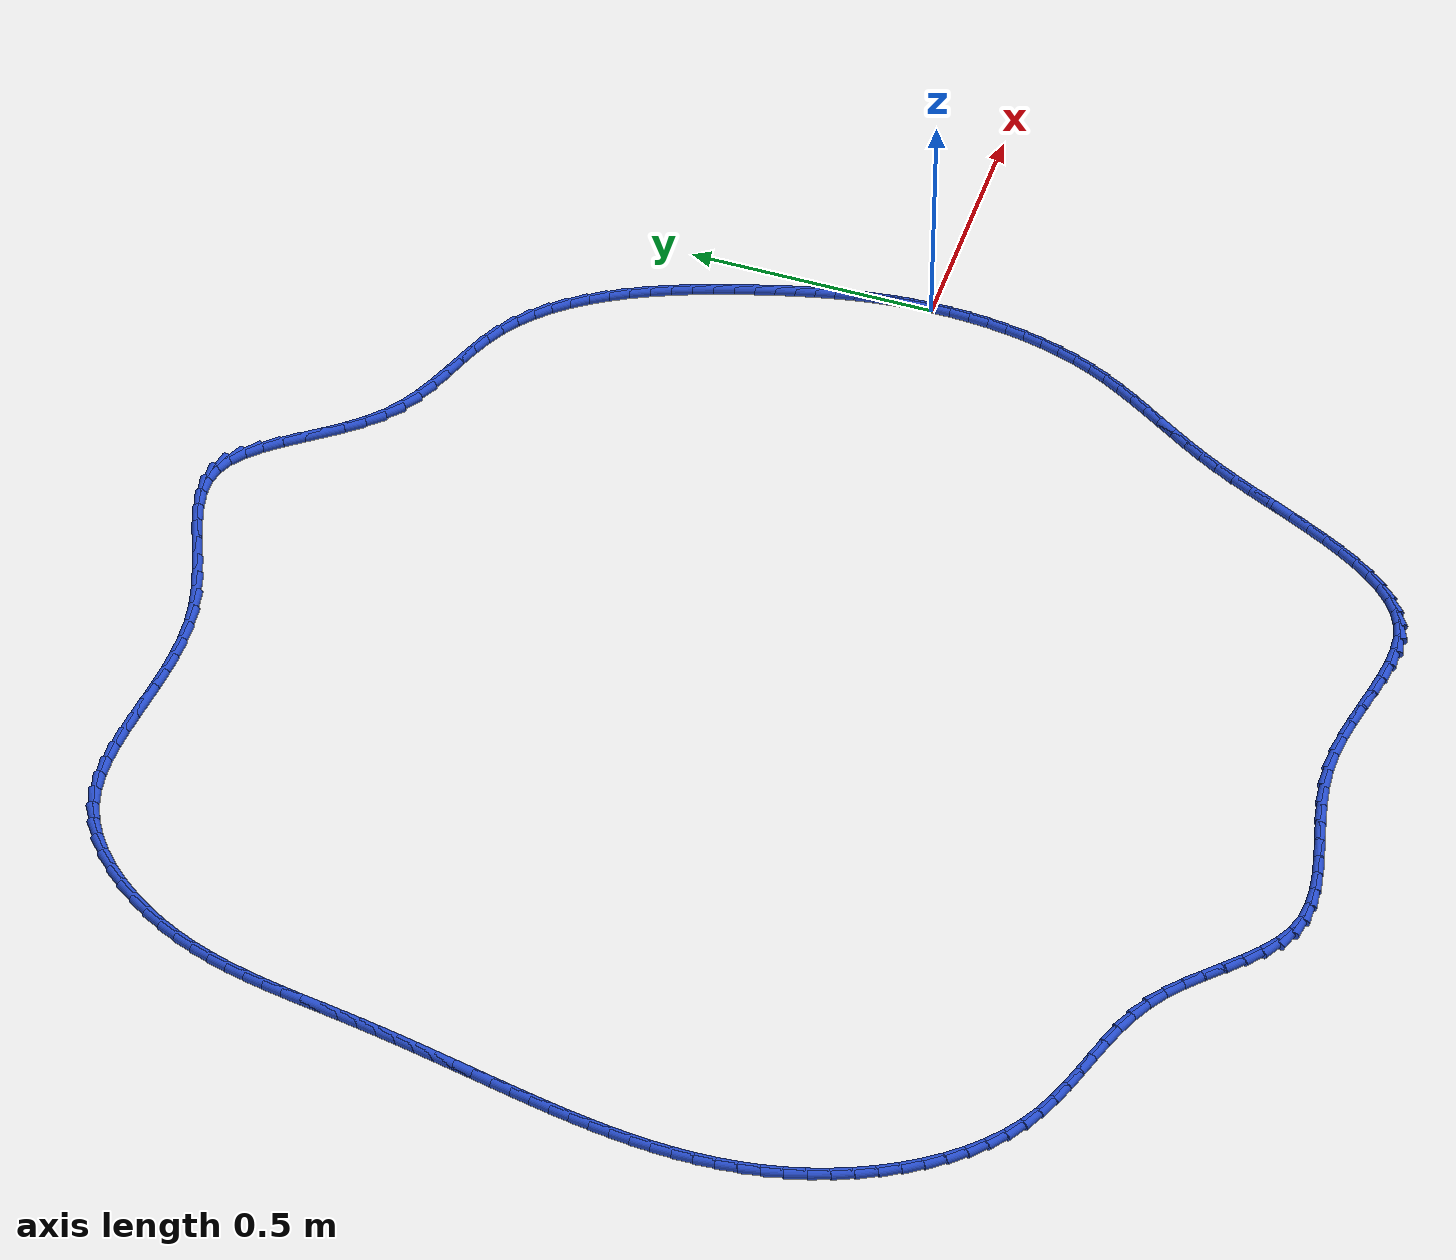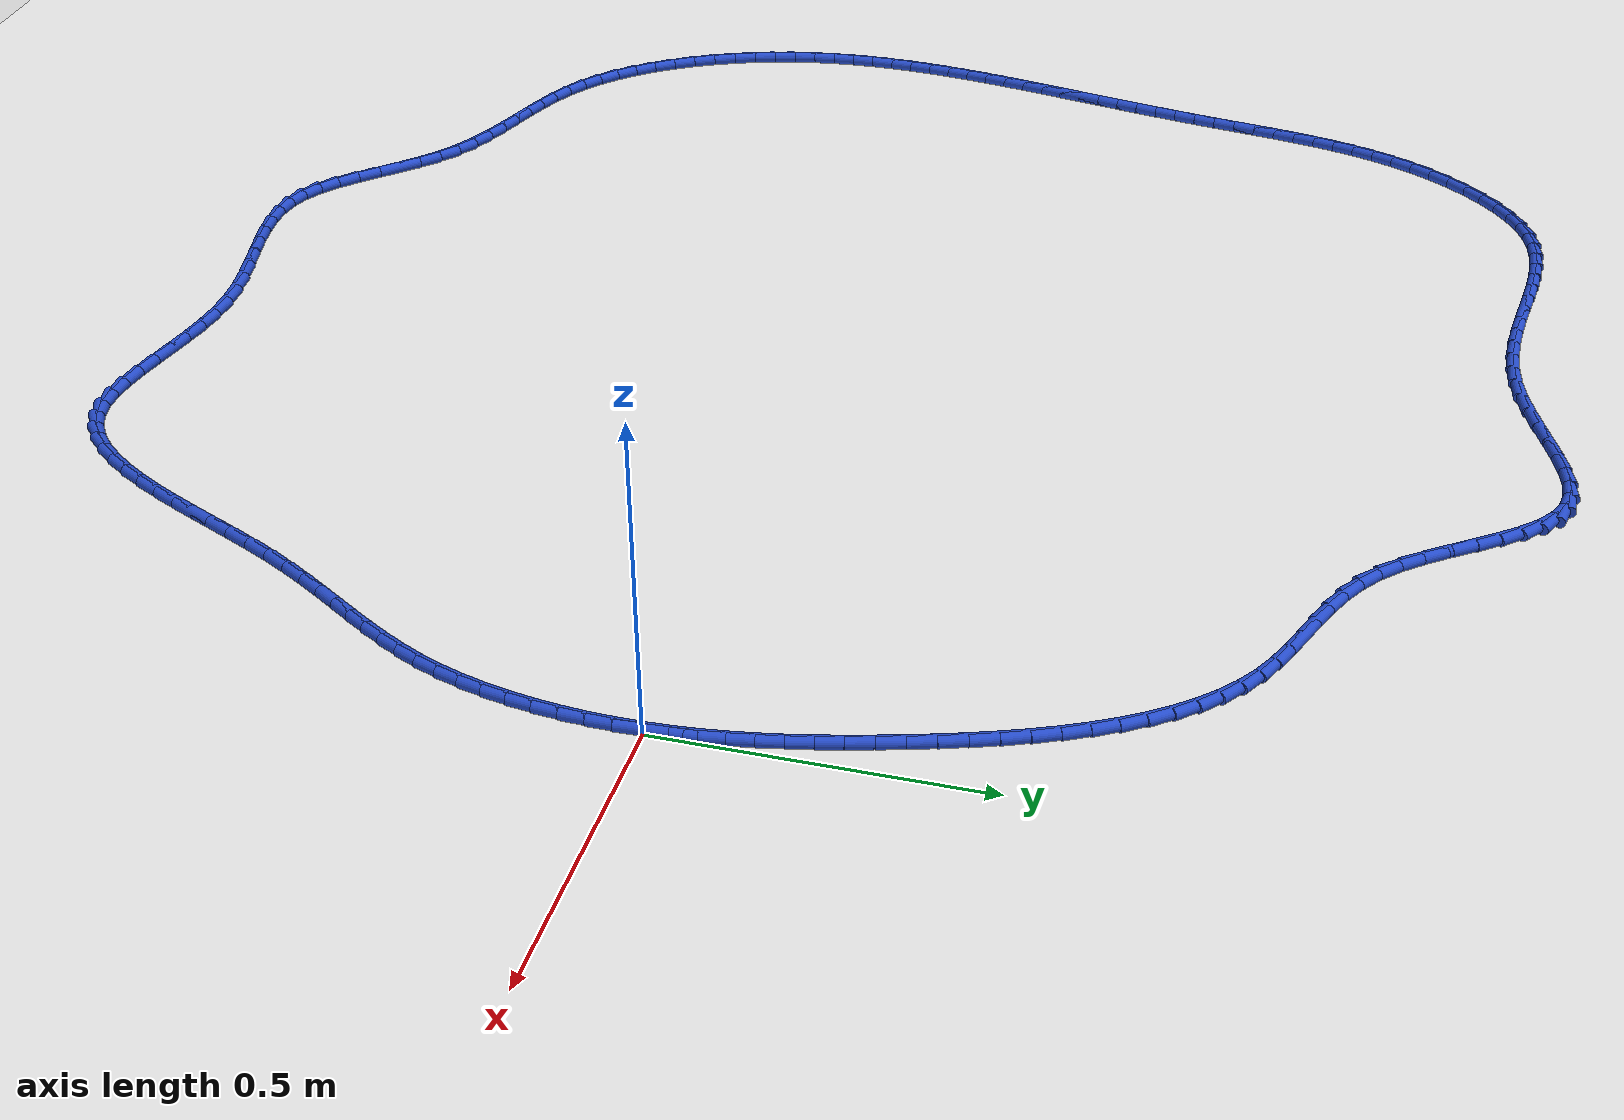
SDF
<sdf version="1.6">
 <world name="default">
  <light name="sun" type="directional">
   <pose>0 0 10 0 -0 0</pose>
   <diffuse>0.8 0.8 0.8 1</diffuse>
   <specular>0.2 0.2 0.2 1</specular>
   <attenuation>
    <range>1000</range>
    <constant>0.9</constant>
    <linear>0.01</linear>
    <quadratic>0.001</quadratic>
   </attenuation>
   <direction>-0.5 0.1 -0.9</direction>
  </light>
  <model name="ground_plane">
   <static>1</static>
   <link name="link">
    <collision name="collision">
     <geometry><plane><normal>0 0 1</normal><size>100 100</size></plane></geometry>
     <surface><friction><ode><mu>100</mu><mu2>50</mu2></ode></friction></surface>
    </collision>
    <visual name="visual">
     <cast_shadows>0</cast_shadows>
     <geometry><plane><normal>0 0 1</normal><size>100 100</size></plane></geometry>
     <material>
      <script><uri>file://media/materials/scripts/gazebo.material</uri><name>Gazebo/WhiteGlow</name></script>
     </material>
    </visual>
   </link>
  </model>
  <gravity>0 0 -9.8</gravity>
  <magnetic_field>6e-06 2.3e-05 -4.2e-05</magnetic_field>
  <atmosphere type="adiabatic"/>
  <physics name="default_physics" default="0" type="ode">
   <max_step_size>0.001</max_step_size>
   <real_time_factor>1</real_time_factor>
   <real_time_update_rate>1000</real_time_update_rate>
  </physics>
  <scene><ambient>0.4 0.4 0.4 1</ambient><background>0.7 0.7 0.7 1</background><shadows>1</shadows></scene>
  <spherical_coordinates>
   <surface_model>EARTH_WGS84</surface_model>
   <latitude_deg>0</latitude_deg>
   <longitude_deg>0</longitude_deg>
   <elevation>0</elevation>
   <heading_deg>0</heading_deg>
  </spherical_coordinates>
  <model name="line">
   <link name="link_0">
    <pose>1.5612511283791264e-17 -1.1102230246251565e-16 0.01 0 1.57 -1.5275932982898037</pose>
    <collision name="collision">
     <geometry><cylinder><radius>0.01</radius><length>0.08</length></cylinder></geometry>
    </collision>
    <visual name="visual">
     <material>
      <script><name>Gazebo/Blue</name><uri>file://media/materials/scripts/gazebo.material</uri></script>
     </material>
     <geometry><cylinder><radius>0.01</radius><length>0.08</length></cylinder></geometry>
    </visual>
   </link>
   <link name="link_1">
    <pose>-0.001700698081941697 0.03934075666589168 0.01 0 1.57 -1.487673856206493</pose>
    <collision name="collision">
     <geometry><cylinder><radius>0.01</radius><length>0.08</length></cylinder></geometry>
    </collision>
    <visual name="visual">
     <material>
      <script><name>Gazebo/Blue</name><uri>file://media/materials/scripts/gazebo.material</uri></script>
     </material>
     <geometry><cylinder><radius>0.01</radius><length>0.08</length></cylinder></geometry>
    </visual>
   </link>
   <link name="link_2">
    <pose>-0.004948036254716881 0.07831765074993403 0.01 0 1.57 -1.450146105756169</pose>
    <collision name="collision">
     <geometry><cylinder><radius>0.01</radius><length>0.08</length></cylinder></geometry>
    </collision>
    <visual name="visual">
     <material>
      <script><name>Gazebo/Blue</name><uri>file://media/materials/scripts/gazebo.material</uri></script>
     </material>
     <geometry><cylinder><radius>0.01</radius><length>0.08</length></cylinder></geometry>
    </visual>
   </link>
   <link name="link_3">
    <pose>-0.009642300428221659 0.11703672382275872 0.01 0 1.57 -1.4154114310185126</pose>
    <collision name="collision">
     <geometry><cylinder><radius>0.01</radius><length>0.08</length></cylinder></geometry>
    </collision>
    <visual name="visual">
     <material>
      <script><name>Gazebo/Blue</name><uri>file://media/materials/scripts/gazebo.material</uri></script>
     </material>
     <geometry><cylinder><radius>0.01</radius><length>0.08</length></cylinder></geometry>
    </visual>
   </link>
   <link name="link_4">
    <pose>-0.01568377651235217 0.15560401745499755 0.01 0 1.57 -1.3837891874943278</pose>
    <collision name="collision">
     <geometry><cylinder><radius>0.01</radius><length>0.08</length></cylinder></geometry>
    </collision>
    <visual name="visual">
     <material>
      <script><name>Gazebo/Blue</name><uri>file://media/materials/scripts/gazebo.material</uri></script>
     </material>
     <geometry><cylinder><radius>0.01</radius><length>0.08</length></cylinder></geometry>
    </visual>
   </link>
   <link name="link_5">
    <pose>-0.02297275041700454 0.19412557321728222 0.01 0 1.57 -1.3555134308795533</pose>
    <collision name="collision">
     <geometry><cylinder><radius>0.01</radius><length>0.08</length></cylinder></geometry>
    </collision>
    <visual name="visual">
     <material>
      <script><name>Gazebo/Blue</name><uri>file://media/materials/scripts/gazebo.material</uri></script>
     </material>
     <geometry><cylinder><radius>0.01</radius><length>0.08</length></cylinder></geometry>
    </visual>
   </link>
   <link name="link_6">
    <pose>-0.03140950805207488 0.23270743268024452 0.01 0 1.57 -1.3307355909975573</pose>
    <collision name="collision">
     <geometry><cylinder><radius>0.01</radius><length>0.08</length></cylinder></geometry>
    </collision>
    <visual name="visual">
     <material>
      <script><name>Gazebo/Blue</name><uri>file://media/materials/scripts/gazebo.material</uri></script>
     </material>
     <geometry><cylinder><radius>0.01</radius><length>0.08</length></cylinder></geometry>
    </visual>
   </link>
   <link name="link_7">
    <pose>-0.04089433532745936 0.2714556374145163 0.01 0 1.57 -1.3095314973160979</pose>
    <collision name="collision">
     <geometry><cylinder><radius>0.01</radius><length>0.08</length></cylinder></geometry>
    </collision>
    <visual name="visual">
     <material>
      <script><name>Gazebo/Blue</name><uri>file://media/materials/scripts/gazebo.material</uri></script>
     </material>
     <geometry><cylinder><radius>0.01</radius><length>0.08</length></cylinder></geometry>
    </visual>
   </link>
   <link name="link_8">
    <pose>-0.05132751815305407 0.31047622899072924 0.01 0 1.57 -1.291900685610605</pose>
    <collision name="collision">
     <geometry><cylinder><radius>0.01</radius><length>0.08</length></cylinder></geometry>
    </collision>
    <visual name="visual">
     <material>
      <script><name>Gazebo/Blue</name><uri>file://media/materials/scripts/gazebo.material</uri></script>
     </material>
     <geometry><cylinder><radius>0.01</radius><length>0.08</length></cylinder></geometry>
    </visual>
   </link>
   <link name="link_9">
    <pose>-0.06260963347442558 0.34987472585825974 0.01 0 1.57 -1.2755632152967689</pose>
    <collision name="collision">
     <geometry><cylinder><radius>0.01</radius><length>0.08</length></cylinder></geometry>
    </collision>
    <visual name="visual">
     <material>
      <script><name>Gazebo/Blue</name><uri>file://media/materials/scripts/gazebo.material</uri></script>
     </material>
     <geometry><cylinder><radius>0.01</radius><length>0.08</length></cylinder></geometry>
    </visual>
   </link>
   <link name="link_10">
    <pose>-0.07470416861009979 0.3896435683917727 0.01 0 1.57 -1.2554088576671867</pose>
    <collision name="collision">
     <geometry><cylinder><radius>0.01</radius><length>0.08</length></cylinder></geometry>
    </collision>
    <visual name="visual">
     <material>
      <script><name>Gazebo/Blue</name><uri>file://media/materials/scripts/gazebo.material</uri></script>
     </material>
     <geometry><cylinder><radius>0.01</radius><length>0.08</length></cylinder></geometry>
    </visual>
   </link>
   <link name="link_11">
    <pose>-0.08771557155818603 0.4295218275849005 0.01 0 1.57 -1.2305443111355374</pose>
    <collision name="collision">
     <geometry><cylinder><radius>0.01</radius><length>0.08</length></cylinder></geometry>
    </collision>
    <visual name="visual">
     <material>
      <script><name>Gazebo/Blue</name><uri>file://media/materials/scripts/gazebo.material</uri></script>
     </material>
     <geometry><cylinder><radius>0.01</radius><length>0.08</length></cylinder></geometry>
    </visual>
   </link>
   <link name="link_12">
    <pose>-0.10176745645254026 0.46921412431394227 0.01 0 1.57 -1.2006301663532073</pose>
    <collision name="collision">
     <geometry><cylinder><radius>0.01</radius><length>0.08</length></cylinder></geometry>
    </collision>
    <visual name="visual">
     <material>
      <script><name>Gazebo/Blue</name><uri>file://media/materials/scripts/gazebo.material</uri></script>
     </material>
     <geometry><cylinder><radius>0.01</radius><length>0.08</length></cylinder></geometry>
    </visual>
   </link>
   <link name="link_13">
    <pose>-0.1169834374270185 0.5084250794551981 0.01 0 1.57 -1.1652040712181195</pose>
    <collision name="collision">
     <geometry><cylinder><radius>0.01</radius><length>0.08</length></cylinder></geometry>
    </collision>
    <visual name="visual">
     <material>
      <script><name>Gazebo/Blue</name><uri>file://media/materials/scripts/gazebo.material</uri></script>
     </material>
     <geometry><cylinder><radius>0.01</radius><length>0.08</length></cylinder></geometry>
    </visual>
   </link>
   <link name="link_14">
    <pose>-0.13348712861547654 0.5468593138849668 0.01 0 1.57 -1.1236855883400392</pose>
    <collision name="collision">
     <geometry><cylinder><radius>0.01</radius><length>0.08</length></cylinder></geometry>
    </collision>
    <visual name="visual">
     <material>
      <script><name>Gazebo/Blue</name><uri>file://media/materials/scripts/gazebo.material</uri></script>
     </material>
     <geometry><cylinder><radius>0.01</radius><length>0.08</length></cylinder></geometry>
    </visual>
   </link>
   <link name="link_15">
    <pose>-0.15140214415177053 0.5842214484795485 0.01 0 1.57 -1.075386920775524</pose>
    <collision name="collision">
     <geometry><cylinder><radius>0.01</radius><length>0.08</length></cylinder></geometry>
    </collision>
    <visual name="visual">
     <material>
      <script><name>Gazebo/Blue</name><uri>file://media/materials/scripts/gazebo.material</uri></script>
     </material>
     <geometry><cylinder><radius>0.01</radius><length>0.08</length></cylinder></geometry>
    </visual>
   </link>
   <link name="link_16">
    <pose>-0.17085209816975627 0.6202161041152425 0.01 0 1.57 -1.0195376406558743</pose>
    <collision name="collision">
     <geometry><cylinder><radius>0.01</radius><length>0.08</length></cylinder></geometry>
    </collision>
    <visual name="visual">
     <material>
      <script><name>Gazebo/Blue</name><uri>file://media/materials/scripts/gazebo.material</uri></script>
     </material>
     <geometry><cylinder><radius>0.01</radius><length>0.08</length></cylinder></geometry>
    </visual>
   </link>
   <link name="link_17">
    <pose>-0.1919606048032897 0.6545479016683481 0.01 0 1.57 -0.9553349598616356</pose>
    <collision name="collision">
     <geometry><cylinder><radius>0.01</radius><length>0.08</length></cylinder></geometry>
    </collision>
    <visual name="visual">
     <material>
      <script><name>Gazebo/Blue</name><uri>file://media/materials/scripts/gazebo.material</uri></script>
     </material>
     <geometry><cylinder><radius>0.01</radius><length>0.08</length></cylinder></geometry>
    </visual>
   </link>
   <link name="link_18">
    <pose>-0.21485127818622693 0.6869214620151652 0.01 0 1.57 -0.8820342935948002</pose>
    <collision name="collision">
     <geometry><cylinder><radius>0.01</radius><length>0.08</length></cylinder></geometry>
    </collision>
    <visual name="visual">
     <material>
      <script><name>Gazebo/Blue</name><uri>file://media/materials/scripts/gazebo.material</uri></script>
     </material>
     <geometry><cylinder><radius>0.01</radius><length>0.08</length></cylinder></geometry>
    </visual>
   </link>
   <link name="link_19">
    <pose>-0.23964773245242377 0.7170414060319935 0.01 0 1.57 -0.7990947910628918</pose>
    <collision name="collision">
     <geometry><cylinder><radius>0.01</radius><length>0.08</length></cylinder></geometry>
    </collision>
    <visual name="visual">
     <material>
      <script><name>Gazebo/Blue</name><uri>file://media/materials/scripts/gazebo.material</uri></script>
     </material>
     <geometry><cylinder><radius>0.01</radius><length>0.08</length></cylinder></geometry>
    </visual>
   </link>
   <link name="link_20">
    <pose>-0.2664735817357364 0.744612354595132 0.01 0 1.57 -0.706385082721863</pose>
    <collision name="collision">
     <geometry><cylinder><radius>0.01</radius><length>0.08</length></cylinder></geometry>
    </collision>
    <visual name="visual">
     <material>
      <script><name>Gazebo/Blue</name><uri>file://media/materials/scripts/gazebo.material</uri></script>
     </material>
     <geometry><cylinder><radius>0.01</radius><length>0.08</length></cylinder></geometry>
    </visual>
   </link>
   <link name="link_21">
    <pose>-0.29545244017002037 0.7693389285808805 0.01 0 1.57 -0.6044279993705203</pose>
    <collision name="collision">
     <geometry><cylinder><radius>0.01</radius><length>0.08</length></cylinder></geometry>
    </collision>
    <visual name="visual">
     <material>
      <script><name>Gazebo/Blue</name><uri>file://media/materials/scripts/gazebo.material</uri></script>
     </material>
     <geometry><cylinder><radius>0.01</radius><length>0.08</length></cylinder></geometry>
    </visual>
   </link>
   <link name="link_22">
    <pose>-0.326707921889132 0.7909257488655386 0.01 0 1.57 -0.4981987468423412</pose>
    <collision name="collision">
     <geometry><cylinder><radius>0.01</radius><length>0.08</length></cylinder></geometry>
    </collision>
    <visual name="visual">
     <material>
      <script><name>Gazebo/Blue</name><uri>file://media/materials/scripts/gazebo.material</uri></script>
     </material>
     <geometry><cylinder><radius>0.01</radius><length>0.08</length></cylinder></geometry>
    </visual>
   </link>
   <link name="link_23">
    <pose>-0.36029703117814027 0.8091970808056621 0.01 0 1.57 -0.4160917837494246</pose>
    <collision name="collision">
     <geometry><cylinder><radius>0.01</radius><length>0.08</length></cylinder></geometry>
    </collision>
    <visual name="visual">
     <material>
      <script><name>Gazebo/Blue</name><uri>file://media/materials/scripts/gazebo.material</uri></script>
     </material>
     <geometry><cylinder><radius>0.01</radius><length>0.08</length></cylinder></geometry>
    </visual>
   </link>
   <link name="link_24">
    <pose>-0.3957767527798784 0.8248753238826917 0.01 0 1.57 -0.3695490540707796</pose>
    <collision name="collision">
     <geometry><cylinder><radius>0.01</radius><length>0.08</length></cylinder></geometry>
    </collision>
    <visual name="visual">
     <material>
      <script><name>Gazebo/Blue</name><uri>file://media/materials/scripts/gazebo.material</uri></script>
     </material>
     <geometry><cylinder><radius>0.01</radius><length>0.08</length></cylinder></geometry>
    </visual>
   </link>
   <link name="link_25">
    <pose>-0.4324768998260011 0.8390909227822458 0.01 0 1.57 -0.35681518918660643</pose>
    <collision name="collision">
     <geometry><cylinder><radius>0.01</radius><length>0.08</length></cylinder></geometry>
    </collision>
    <visual name="visual">
     <material>
      <script><name>Gazebo/Blue</name><uri>file://media/materials/scripts/gazebo.material</uri></script>
     </material>
     <geometry><cylinder><radius>0.01</radius><length>0.08</length></cylinder></geometry>
    </visual>
   </link>
   <link name="link_26">
    <pose>-0.46972614661818374 0.8529763677541273 0.01 0 1.57 -0.37671525680773915</pose>
    <collision name="collision">
     <geometry><cylinder><radius>0.01</radius><length>0.08</length></cylinder></geometry>
    </collision>
    <visual name="visual">
     <material>
      <script><name>Gazebo/Blue</name><uri>file://media/materials/scripts/gazebo.material</uri></script>
     </material>
     <geometry><cylinder><radius>0.01</radius><length>0.08</length></cylinder></geometry>
    </visual>
   </link>
   <link name="link_27">
    <pose>-0.5068531674581008 0.867664149048139 0.01 0 1.57 -0.429074436421221</pose>
    <collision name="collision">
     <geometry><cylinder><radius>0.01</radius><length>0.08</length></cylinder></geometry>
    </collision>
    <visual name="visual">
     <material>
      <script><name>Gazebo/Blue</name><uri>file://media/materials/scripts/gazebo.material</uri></script>
     </material>
     <geometry><cylinder><radius>0.01</radius><length>0.08</length></cylinder></geometry>
    </visual>
   </link>
   <link name="link_28">
    <pose>-0.5431866366474281 0.8842867569140839 0.01 0 1.57 -0.5140510791788202</pose>
    <collision name="collision">
     <geometry><cylinder><radius>0.01</radius><length>0.08</length></cylinder></geometry>
    </collision>
    <visual name="visual">
     <material>
      <script><name>Gazebo/Blue</name><uri>file://media/materials/scripts/gazebo.material</uri></script>
     </material>
     <geometry><cylinder><radius>0.01</radius><length>0.08</length></cylinder></geometry>
    </visual>
   </link>
   <link name="link_29">
    <pose>-0.5780552284878403 0.9039766816017649 0.01 0 1.57 -0.6304796986592119</pose>
    <collision name="collision">
     <geometry><cylinder><radius>0.01</radius><length>0.08</length></cylinder></geometry>
    </collision>
    <visual name="visual">
     <material>
      <script><name>Gazebo/Blue</name><uri>file://media/materials/scripts/gazebo.material</uri></script>
     </material>
     <geometry><cylinder><radius>0.01</radius><length>0.08</length></cylinder></geometry>
    </visual>
   </link>
   <link name="link_30">
    <pose>-0.6107876199701913 0.9278664076006508 0.01 0 1.57 -0.7613870550782723</pose>
    <collision name="collision">
     <geometry><cylinder><radius>0.01</radius><length>0.08</length></cylinder></geometry>
    </collision>
    <visual name="visual">
     <material>
      <script><name>Gazebo/Blue</name><uri>file://media/materials/scripts/gazebo.material</uri></script>
     </material>
     <geometry><cylinder><radius>0.01</radius><length>0.08</length></cylinder></geometry>
    </visual>
   </link>
   <link name="link_31">
    <pose>-0.6409388978767352 0.9566034401100839 0.01 0 1.57 -0.8590058676684904</pose>
    <collision name="collision">
     <geometry><cylinder><radius>0.01</radius><length>0.08</length></cylinder></geometry>
    </collision>
    <visual name="visual">
     <material>
      <script><name>Gazebo/Blue</name><uri>file://media/materials/scripts/gazebo.material</uri></script>
     </material>
     <geometry><cylinder><radius>0.01</radius><length>0.08</length></cylinder></geometry>
    </visual>
   </link>
   <link name="link_32">
    <pose>-0.6689085603835728 0.9890265196296606 0.01 0 1.57 -0.9182802615396253</pose>
    <collision name="collision">
     <geometry><cylinder><radius>0.01</radius><length>0.08</length></cylinder></geometry>
    </collision>
    <visual name="visual">
     <material>
      <script><name>Gazebo/Blue</name><uri>file://media/materials/scripts/gazebo.material</uri></script>
     </material>
     <geometry><cylinder><radius>0.01</radius><length>0.08</length></cylinder></geometry>
    </visual>
   </link>
   <link name="link_33">
    <pose>-0.6952929233646922 1.023552794877033 0.01 0 1.57 -0.9437391704710368</pose>
    <collision name="collision">
     <geometry><cylinder><radius>0.01</radius><length>0.08</length></cylinder></geometry>
    </collision>
    <visual name="visual">
     <material>
      <script><name>Gazebo/Blue</name><uri>file://media/materials/scripts/gazebo.material</uri></script>
     </material>
     <geometry><cylinder><radius>0.01</radius><length>0.08</length></cylinder></geometry>
    </visual>
   </link>
   <link name="link_34">
    <pose>-0.7206883026940815 1.0585994145698525 0.01 0 1.57 -0.9364987608788192</pose>
    <collision name="collision">
     <geometry><cylinder><radius>0.01</radius><length>0.08</length></cylinder></geometry>
    </collision>
    <visual name="visual">
     <material>
      <script><name>Gazebo/Blue</name><uri>file://media/materials/scripts/gazebo.material</uri></script>
     </material>
     <geometry><cylinder><radius>0.01</radius><length>0.08</length></cylinder></geometry>
    </visual>
   </link>
   <link name="link_35">
    <pose>-0.7456910142457293 1.0925835274257716 0.01 0 1.57 -0.893427317606175</pose>
    <collision name="collision">
     <geometry><cylinder><radius>0.01</radius><length>0.08</length></cylinder></geometry>
    </collision>
    <visual name="visual">
     <material>
      <script><name>Gazebo/Blue</name><uri>file://media/materials/scripts/gazebo.material</uri></script>
     </material>
     <geometry><cylinder><radius>0.01</radius><length>0.08</length></cylinder></geometry>
    </visual>
   </link>
   <link name="link_36">
    <pose>-0.770897373893624 1.1239222821624428 0.01 0 1.57 -0.806183701249994</pose>
    <collision name="collision">
     <geometry><cylinder><radius>0.01</radius><length>0.08</length></cylinder></geometry>
    </collision>
    <visual name="visual">
     <material>
      <script><name>Gazebo/Blue</name><uri>file://media/materials/scripts/gazebo.material</uri></script>
     </material>
     <geometry><cylinder><radius>0.01</radius><length>0.08</length></cylinder></geometry>
    </visual>
   </link>
   <link name="link_37">
    <pose>-0.7969036975117537 1.1510328274975175 0.01 0 1.57 -0.6607326906664192</pose>
    <collision name="collision">
     <geometry><cylinder><radius>0.01</radius><length>0.08</length></cylinder></geometry>
    </collision>
    <visual name="visual">
     <material>
      <script><name>Gazebo/Blue</name><uri>file://media/materials/scripts/gazebo.material</uri></script>
     </material>
     <geometry><cylinder><radius>0.01</radius><length>0.08</length></cylinder></geometry>
    </visual>
   </link>
   <link name="link_38">
    <pose>-0.8243063009741065 1.172332312148648 0.01 0 1.57 -0.4418620687028044</pose>
    <collision name="collision">
     <geometry><cylinder><radius>0.01</radius><length>0.08</length></cylinder></geometry>
    </collision>
    <visual name="visual">
     <material>
      <script><name>Gazebo/Blue</name><uri>file://media/materials/scripts/gazebo.material</uri></script>
     </material>
     <geometry><cylinder><radius>0.01</radius><length>0.08</length></cylinder></geometry>
    </visual>
   </link>
   <link name="link_39">
    <pose>-0.8537014899317251 1.1862379206578577 0.01 0 1.57 -0.17140965583437082</pose>
    <collision name="collision">
     <geometry><cylinder><radius>0.01</radius><length>0.08</length></cylinder></geometry>
    </collision>
    <visual name="visual">
     <material>
      <script><name>Gazebo/Blue</name><uri>file://media/materials/scripts/gazebo.material</uri></script>
     </material>
     <geometry><cylinder><radius>0.01</radius><length>0.08</length></cylinder></geometry>
    </visual>
   </link>
   <link name="link_40">
    <pose>-0.8855202924062847 1.191746021601011 0.01 0 1.57 0.05407094459483777</pose>
    <collision name="collision">
     <geometry><cylinder><radius>0.01</radius><length>0.08</length></cylinder></geometry>
    </collision>
    <visual name="visual">
     <material>
      <script><name>Gazebo/Blue</name><uri>file://media/materials/scripts/gazebo.material</uri></script>
     </material>
     <geometry><cylinder><radius>0.01</radius><length>0.08</length></cylinder></geometry>
    </visual>
   </link>
   <link name="link_41">
    <pose>-0.9196093091463209 1.1899009978366097 0.01 0 1.57 0.21031361238165214</pose>
    <collision name="collision">
     <geometry><cylinder><radius>0.01</radius><length>0.08</length></cylinder></geometry>
    </collision>
    <visual name="visual">
     <material>
      <script><name>Gazebo/Blue</name><uri>file://media/materials/scripts/gazebo.material</uri></script>
     </material>
     <geometry><cylinder><radius>0.01</radius><length>0.08</length></cylinder></geometry>
    </visual>
   </link>
   <link name="link_42">
    <pose>-0.9556860264615896 1.1821996892299877 0.01 0 1.57 0.3089955765308184</pose>
    <collision name="collision">
     <geometry><cylinder><radius>0.01</radius><length>0.08</length></cylinder></geometry>
    </collision>
    <visual name="visual">
     <material>
      <script><name>Gazebo/Blue</name><uri>file://media/materials/scripts/gazebo.material</uri></script>
     </material>
     <geometry><cylinder><radius>0.01</radius><length>0.08</length></cylinder></geometry>
    </visual>
   </link>
   <link name="link_43">
    <pose>-0.993467930661846 1.1701389356464786 0.01 0 1.57 0.3637179073982948</pose>
    <collision name="collision">
     <geometry><cylinder><radius>0.01</radius><length>0.08</length></cylinder></geometry>
    </collision>
    <visual name="visual">
     <material>
      <script><name>Gazebo/Blue</name><uri>file://media/materials/scripts/gazebo.material</uri></script>
     </material>
     <geometry><cylinder><radius>0.01</radius><length>0.08</length></cylinder></geometry>
    </visual>
   </link>
   <link name="link_44">
    <pose>-1.032672508056846 1.1552155769514159 0.01 0 1.57 0.3837335945520792</pose>
    <collision name="collision">
     <geometry><cylinder><radius>0.01</radius><length>0.08</length></cylinder></geometry>
    </collision>
    <visual name="visual">
     <material>
      <script><name>Gazebo/Blue</name><uri>file://media/materials/scripts/gazebo.material</uri></script>
     </material>
     <geometry><cylinder><radius>0.01</radius><length>0.08</length></cylinder></geometry>
    </visual>
   </link>
   <link name="link_45">
    <pose>-1.0730172449563455 1.1389264530101346 0.01 0 1.57 0.37373212466682687</pose>
    <collision name="collision">
     <geometry><cylinder><radius>0.01</radius><length>0.08</length></cylinder></geometry>
    </collision>
    <visual name="visual">
     <material>
      <script><name>Gazebo/Blue</name><uri>file://media/materials/scripts/gazebo.material</uri></script>
     </material>
     <geometry><cylinder><radius>0.01</radius><length>0.08</length></cylinder></geometry>
    </visual>
   </link>
   <link name="link_46">
    <pose>-1.1142196276701002 1.1227684036879675 0.01 0 1.57 0.33471175437687406</pose>
    <collision name="collision">
     <geometry><cylinder><radius>0.01</radius><length>0.08</length></cylinder></geometry>
    </collision>
    <visual name="visual">
     <material>
      <script><name>Gazebo/Blue</name><uri>file://media/materials/scripts/gazebo.material</uri></script>
     </material>
     <geometry><cylinder><radius>0.01</radius><length>0.08</length></cylinder></geometry>
    </visual>
   </link>
   <link name="link_47">
    <pose>-1.1559971425078657 1.108238268850249 0.01 0 1.57 0.264741006083092</pose>
    <collision name="collision">
     <geometry><cylinder><radius>0.01</radius><length>0.08</length></cylinder></geometry>
    </collision>
    <visual name="visual">
     <material>
      <script><name>Gazebo/Blue</name><uri>file://media/materials/scripts/gazebo.material</uri></script>
     </material>
     <geometry><cylinder><radius>0.01</radius><length>0.08</length></cylinder></geometry>
    </visual>
   </link>
   <link name="link_48">
    <pose>-1.1980672776987353 1.0968328656514157 0.01 0 1.57 0.16935201622822105</pose>
    <collision name="collision">
     <geometry><cylinder><radius>0.01</radius><length>0.08</length></cylinder></geometry>
    </collision>
    <visual name="visual">
     <material>
      <script><name>Gazebo/Blue</name><uri>file://media/materials/scripts/gazebo.material</uri></script>
     </material>
     <geometry><cylinder><radius>0.01</radius><length>0.08</length></cylinder></geometry>
    </visual>
   </link>
   <link name="link_49">
    <pose>-1.2401828027273871 1.089631539651165 0.01 0 1.57 0.08074902936610112</pose>
    <collision name="collision">
     <geometry><cylinder><radius>0.01</radius><length>0.08</length></cylinder></geometry>
    </collision>
    <visual name="visual">
     <material>
      <script><name>Gazebo/Blue</name><uri>file://media/materials/scripts/gazebo.material</uri></script>
     </material>
     <geometry><cylinder><radius>0.01</radius><length>0.08</length></cylinder></geometry>
    </visual>
   </link>
   <link name="link_50">
    <pose>-1.2822219119328608 1.0862295249992515 0.01 0 1.57 0.008051624661811831</pose>
    <collision name="collision">
     <geometry><cylinder><radius>0.01</radius><length>0.08</length></cylinder></geometry>
    </collision>
    <visual name="visual">
     <material>
      <script><name>Gazebo/Blue</name><uri>file://media/materials/scripts/gazebo.material</uri></script>
     </material>
     <geometry><cylinder><radius>0.01</radius><length>0.08</length></cylinder></geometry>
    </visual>
   </link>
   <link name="link_51">
    <pose>-1.3240906589164114 1.0858924062784632 0.01 0 1.57 -0.047875627217613244</pose>
    <collision name="collision">
     <geometry><cylinder><radius>0.01</radius><length>0.08</length></cylinder></geometry>
    </collision>
    <visual name="visual">
     <material>
      <script><name>Gazebo/Blue</name><uri>file://media/materials/scripts/gazebo.material</uri></script>
     </material>
     <geometry><cylinder><radius>0.01</radius><length>0.08</length></cylinder></geometry>
    </visual>
   </link>
   <link name="link_52">
    <pose>-1.3656950972792952 1.0878857680715892 0.01 0 1.57 -0.08680576806463255</pose>
    <collision name="collision">
     <geometry><cylinder><radius>0.01</radius><length>0.08</length></cylinder></geometry>
    </collision>
    <visual name="visual">
     <material>
      <script><name>Gazebo/Blue</name><uri>file://media/materials/scripts/gazebo.material</uri></script>
     </material>
     <geometry><cylinder><radius>0.01</radius><length>0.08</length></cylinder></geometry>
    </visual>
   </link>
   <link name="link_53">
    <pose>-1.4069412806227661 1.0914751949614188 0.01 0 1.57 -0.10868117719124837</pose>
    <collision name="collision">
     <geometry><cylinder><radius>0.01</radius><length>0.08</length></cylinder></geometry>
    </collision>
    <visual name="visual">
     <material>
      <script><name>Gazebo/Blue</name><uri>file://media/materials/scripts/gazebo.material</uri></script>
     </material>
     <geometry><cylinder><radius>0.01</radius><length>0.08</length></cylinder></geometry>
    </visual>
   </link>
   <link name="link_54">
    <pose>-1.4477352625480802 1.0959262715307403 0.01 0 1.57 -0.11326610394453168</pose>
    <collision name="collision">
     <geometry><cylinder><radius>0.01</radius><length>0.08</length></cylinder></geometry>
    </collision>
    <visual name="visual">
     <material>
      <script><name>Gazebo/Blue</name><uri>file://media/materials/scripts/gazebo.material</uri></script>
     </material>
     <geometry><cylinder><radius>0.01</radius><length>0.08</length></cylinder></geometry>
    </visual>
   </link>
   <link name="link_55">
    <pose>-1.4879830966564933 1.1005045823623432 0.01 0 1.57 -0.09992751326492197</pose>
    <collision name="collision">
     <geometry><cylinder><radius>0.01</radius><length>0.08</length></cylinder></geometry>
    </collision>
    <visual name="visual">
     <material>
      <script><name>Gazebo/Blue</name><uri>file://media/materials/scripts/gazebo.material</uri></script>
     </material>
     <geometry><cylinder><radius>0.01</radius><length>0.08</length></cylinder></geometry>
    </visual>
   </link>
   <link name="link_56">
    <pose>-1.5275908365492599 1.1044757120390167 0.01 0 1.57 -0.06754010004169966</pose>
    <collision name="collision">
     <geometry><cylinder><radius>0.01</radius><length>0.08</length></cylinder></geometry>
    </collision>
    <visual name="visual">
     <material>
      <script><name>Gazebo/Blue</name><uri>file://media/materials/scripts/gazebo.material</uri></script>
     </material>
     <geometry><cylinder><radius>0.01</radius><length>0.08</length></cylinder></geometry>
    </visual>
   </link>
   <link name="link_57">
    <pose>-1.5664645358276357 1.1071052451435492 0.01 0 1.57 -0.014547817159745936</pose>
    <collision name="collision">
     <geometry><cylinder><radius>0.01</radius><length>0.08</length></cylinder></geometry>
    </collision>
    <visual name="visual">
     <material>
      <script><name>Gazebo/Blue</name><uri>file://media/materials/scripts/gazebo.material</uri></script>
     </material>
     <geometry><cylinder><radius>0.01</radius><length>0.08</length></cylinder></geometry>
    </visual>
   </link>
   <link name="link_58">
    <pose>-1.6045102480928757 1.1076587662587294 0.01 0 1.57 0.06071935727759957</pose>
    <collision name="collision">
     <geometry><cylinder><radius>0.01</radius><length>0.08</length></cylinder></geometry>
    </collision>
    <visual name="visual">
     <material>
      <script><name>Gazebo/Blue</name><uri>file://media/materials/scripts/gazebo.material</uri></script>
     </material>
     <geometry><cylinder><radius>0.01</radius><length>0.08</length></cylinder></geometry>
    </visual>
   </link>
   <link name="link_59">
    <pose>-1.6416340269462353 1.1054018599673467 0.01 0 1.57 0.15931637965256634</pose>
    <collision name="collision">
     <geometry><cylinder><radius>0.01</radius><length>0.08</length></cylinder></geometry>
    </collision>
    <visual name="visual">
     <material>
      <script><name>Gazebo/Blue</name><uri>file://media/materials/scripts/gazebo.material</uri></script>
     </material>
     <geometry><cylinder><radius>0.01</radius><length>0.08</length></cylinder></geometry>
    </visual>
   </link>
   <link name="link_60">
    <pose>-1.6777419259889705 1.0996001108521902 0.01 0 1.57 0.2804528105075971</pose>
    <collision name="collision">
     <geometry><cylinder><radius>0.01</radius><length>0.08</length></cylinder></geometry>
    </collision>
    <visual name="visual">
     <material>
      <script><name>Gazebo/Blue</name><uri>file://media/materials/scripts/gazebo.material</uri></script>
     </material>
     <geometry><cylinder><radius>0.01</radius><length>0.08</length></cylinder></geometry>
    </visual>
   </link>
   <link name="link_61">
    <pose>-1.712739998822336 1.0895191034960487 0.01 0 1.57 0.41875540404414924</pose>
    <collision name="collision">
     <geometry><cylinder><radius>0.01</radius><length>0.08</length></cylinder></geometry>
    </collision>
    <visual name="visual">
     <material>
      <script><name>Gazebo/Blue</name><uri>file://media/materials/scripts/gazebo.material</uri></script>
     </material>
     <geometry><cylinder><radius>0.01</radius><length>0.08</length></cylinder></geometry>
    </visual>
   </link>
   <link name="link_62">
    <pose>-1.746529670922118 1.0744799768860425 0.01 0 1.57 0.5511339803849232</pose>
    <collision name="collision">
     <geometry><cylinder><radius>0.01</radius><length>0.08</length></cylinder></geometry>
    </collision>
    <visual name="visual">
     <material>
      <script><name>Gazebo/Blue</name><uri>file://media/materials/scripts/gazebo.material</uri></script>
     </material>
     <geometry><cylinder><radius>0.01</radius><length>0.08</length></cylinder></geometry>
    </visual>
   </link>
   <link name="link_63">
    <pose>-1.7789500198035857 1.0545522731870298 0.01 0 1.57 0.6654593873830869</pose>
    <collision name="collision">
     <geometry><cylinder><radius>0.01</radius><length>0.08</length></cylinder></geometry>
    </collision>
    <visual name="visual">
     <material>
      <script><name>Gazebo/Blue</name><uri>file://media/materials/scripts/gazebo.material</uri></script>
     </material>
     <geometry><cylinder><radius>0.01</radius><length>0.08</length></cylinder></geometry>
    </visual>
   </link>
   <link name="link_64">
    <pose>-1.8097954295287273 1.0303420191927137 0.01 0 1.57 0.7645227738309321</pose>
    <collision name="collision">
     <geometry><cylinder><radius>0.01</radius><length>0.08</length></cylinder></geometry>
    </collision>
    <visual name="visual">
     <material>
      <script><name>Gazebo/Blue</name><uri>file://media/materials/scripts/gazebo.material</uri></script>
     </material>
     <geometry><cylinder><radius>0.01</radius><length>0.08</length></cylinder></geometry>
    </visual>
   </link>
   <link name="link_65">
    <pose>-1.8388593100612947 1.0024669344323895 0.01 0 1.57 0.8516213610013983</pose>
    <collision name="collision">
     <geometry><cylinder><radius>0.01</radius><length>0.08</length></cylinder></geometry>
    </collision>
    <visual name="visual">
     <material>
      <script><name>Gazebo/Blue</name><uri>file://media/materials/scripts/gazebo.material</uri></script>
     </material>
     <geometry><cylinder><radius>0.01</radius><length>0.08</length></cylinder></geometry>
    </visual>
   </link>
   <link name="link_66">
    <pose>-1.8659350713650393 0.9715447384353533 0.01 0 1.57 0.9298453504984128</pose>
    <collision name="collision">
     <geometry><cylinder><radius>0.01</radius><length>0.08</length></cylinder></geometry>
    </collision>
    <visual name="visual">
     <material>
      <script><name>Gazebo/Blue</name><uri>file://media/materials/scripts/gazebo.material</uri></script>
     </material>
     <geometry><cylinder><radius>0.01</radius><length>0.08</length></cylinder></geometry>
    </visual>
   </link>
   <link name="link_67">
    <pose>-1.8908161234037106 0.9381931507309005 0.01 0 1.57 1.0019822968421306</pose>
    <collision name="collision">
     <geometry><cylinder><radius>0.01</radius><length>0.08</length></cylinder></geometry>
    </collision>
    <visual name="visual">
     <material>
      <script><name>Gazebo/Blue</name><uri>file://media/materials/scripts/gazebo.material</uri></script>
     </material>
     <geometry><cylinder><radius>0.01</radius><length>0.08</length></cylinder></geometry>
    </visual>
   </link>
   <link name="link_68">
    <pose>-1.9132958761410612 0.9030298908483266 0.01 0 1.57 1.0705881719301298</pose>
    <collision name="collision">
     <geometry><cylinder><radius>0.01</radius><length>0.08</length></cylinder></geometry>
    </collision>
    <visual name="visual">
     <material>
      <script><name>Gazebo/Blue</name><uri>file://media/materials/scripts/gazebo.material</uri></script>
     </material>
     <geometry><cylinder><radius>0.01</radius><length>0.08</length></cylinder></geometry>
    </visual>
   </link>
   <link name="link_69">
    <pose>-1.933167739540842 0.8666726783169272 0.01 0 1.57 1.1374752683741867</pose>
    <collision name="collision">
     <geometry><cylinder><radius>0.01</radius><length>0.08</length></cylinder></geometry>
    </collision>
    <visual name="visual">
     <material>
      <script><name>Gazebo/Blue</name><uri>file://media/materials/scripts/gazebo.material</uri></script>
     </material>
     <geometry><cylinder><radius>0.01</radius><length>0.08</length></cylinder></geometry>
    </visual>
   </link>
   <link name="link_70">
    <pose>-1.950283446996872 0.8296774823380398 0.01 0 1.57 1.2000164831362308</pose>
    <collision name="collision">
     <geometry><cylinder><radius>0.01</radius><length>0.08</length></cylinder></geometry>
    </collision>
    <visual name="visual">
     <material>
      <script><name>Gazebo/Blue</name><uri>file://media/materials/scripts/gazebo.material</uri></script>
     </material>
     <geometry><cylinder><radius>0.01</radius><length>0.08</length></cylinder></geometry>
    </visual>
   </link>
   <link name="link_71">
    <pose>-1.9648395218536399 0.7922352234094928 0.01 0 1.57 1.2559958066403862</pose>
    <collision name="collision">
     <geometry><cylinder><radius>0.01</radius><length>0.08</length></cylinder></geometry>
    </collision>
    <visual name="visual">
     <material>
      <script><name>Gazebo/Blue</name><uri>file://media/materials/scripts/gazebo.material</uri></script>
     </material>
     <geometry><cylinder><radius>0.01</radius><length>0.08</length></cylinder></geometry>
    </visual>
   </link>
   <link name="link_72">
    <pose>-1.9771587308760386 0.7544031609497964 0.01 0 1.57 1.3046243806633468</pose>
    <collision name="collision">
     <geometry><cylinder><radius>0.01</radius><length>0.08</length></cylinder></geometry>
    </collision>
    <visual name="visual">
     <material>
      <script><name>Gazebo/Blue</name><uri>file://media/materials/scripts/gazebo.material</uri></script>
     </material>
     <geometry><cylinder><radius>0.01</radius><length>0.08</length></cylinder></geometry>
    </visual>
   </link>
   <link name="link_73">
    <pose>-1.9875640301846924 0.7162383538957917 0.01 0 1.57 1.3453943355236802</pose>
    <collision name="collision">
     <geometry><cylinder><radius>0.01</radius><length>0.08</length></cylinder></geometry>
    </collision>
    <visual name="visual">
     <material>
      <script><name>Gazebo/Blue</name><uri>file://media/materials/scripts/gazebo.material</uri></script>
     </material>
     <geometry><cylinder><radius>0.01</radius><length>0.08</length></cylinder></geometry>
    </visual>
   </link>
   <link name="link_74">
    <pose>-1.9963783759002258 0.6777978611843204 0.01 0 1.57 1.3780181869978718</pose>
    <collision name="collision">
     <geometry><cylinder><radius>0.01</radius><length>0.08</length></cylinder></geometry>
    </collision>
    <visual name="visual">
     <material>
      <script><name>Gazebo/Blue</name><uri>file://media/materials/scripts/gazebo.material</uri></script>
     </material>
     <geometry><cylinder><radius>0.01</radius><length>0.08</length></cylinder></geometry>
    </visual>
   </link>
   <link name="link_75">
    <pose>-2.0039247241432623 0.6391387417522245 0.01 0 1.57 1.4023613540720348</pose>
    <collision name="collision">
     <geometry><cylinder><radius>0.01</radius><length>0.08</length></cylinder></geometry>
    </collision>
    <visual name="visual">
     <material>
      <script><name>Gazebo/Blue</name><uri>file://media/materials/scripts/gazebo.material</uri></script>
     </material>
     <geometry><cylinder><radius>0.01</radius><length>0.08</length></cylinder></geometry>
    </visual>
   </link>
   <link name="link_76">
    <pose>-2.0105260310344275 0.6003180545363457 0.01 0 1.57 1.4183796505299378</pose>
    <collision name="collision">
     <geometry><cylinder><radius>0.01</radius><length>0.08</length></cylinder></geometry>
    </collision>
    <visual name="visual">
     <material>
      <script><name>Gazebo/Blue</name><uri>file://media/materials/scripts/gazebo.material</uri></script>
     </material>
     <geometry><cylinder><radius>0.01</radius><length>0.08</length></cylinder></geometry>
    </visual>
   </link>
   <link name="link_77">
    <pose>-2.016505252694345 0.5613928584735252 0.01 0 1.57 1.4260697138946712</pose>
    <collision name="collision">
     <geometry><cylinder><radius>0.01</radius><length>0.08</length></cylinder></geometry>
    </collision>
    <visual name="visual">
     <material>
      <script><name>Gazebo/Blue</name><uri>file://media/materials/scripts/gazebo.material</uri></script>
     </material>
     <geometry><cylinder><radius>0.01</radius><length>0.08</length></cylinder></geometry>
    </visual>
   </link>
   <link name="link_78">
    <pose>-2.0221853452436394 0.5224202125006054 0.01 0 1.57 1.425435767744703</pose>
    <collision name="collision">
     <geometry><cylinder><radius>0.01</radius><length>0.08</length></cylinder></geometry>
    </collision>
    <visual name="visual">
     <material>
      <script><name>Gazebo/Blue</name><uri>file://media/materials/scripts/gazebo.material</uri></script>
     </material>
     <geometry><cylinder><radius>0.01</radius><length>0.08</length></cylinder></geometry>
    </visual>
   </link>
   <link name="link_79">
    <pose>-2.027889264802934 0.48345717555442774 0.01 0 1.57 1.4169697358094344</pose>
    <collision name="collision">
     <geometry><cylinder><radius>0.01</radius><length>0.08</length></cylinder></geometry>
    </collision>
    <visual name="visual">
     <material>
      <script><name>Gazebo/Blue</name><uri>file://media/materials/scripts/gazebo.material</uri></script>
     </material>
     <geometry><cylinder><radius>0.01</radius><length>0.08</length></cylinder></geometry>
    </visual>
   </link>
   <link name="link_80">
    <pose>-2.0339208390203525 0.4445567183730713 0.01 0 1.57 1.4064179368934326</pose>
    <collision name="collision">
     <geometry><cylinder><radius>0.01</radius><length>0.08</length></cylinder></geometry>
    </collision>
    <visual name="visual">
     <material>
      <script><name>Gazebo/Blue</name><uri>file://media/materials/scripts/gazebo.material</uri></script>
     </material>
     <geometry><cylinder><radius>0.01</radius><length>0.08</length></cylinder></geometry>
    </visual>
   </link>
   <link name="link_81">
    <pose>-2.0403621498495514 0.4057244194904799 0.01 0 1.57 1.3974937586914222</pose>
    <collision name="collision">
     <geometry><cylinder><radius>0.01</radius><length>0.08</length></cylinder></geometry>
    </collision>
    <visual name="visual">
     <material>
      <script><name>Gazebo/Blue</name><uri>file://media/materials/scripts/gazebo.material</uri></script>
     </material>
     <geometry><cylinder><radius>0.01</radius><length>0.08</length></cylinder></geometry>
    </visual>
   </link>
   <link name="link_82">
    <pose>-2.047152512680406 0.3669353449106868 0.01 0 1.57 1.3902678403352844</pose>
    <collision name="collision">
     <geometry><cylinder><radius>0.01</radius><length>0.08</length></cylinder></geometry>
    </collision>
    <visual name="visual">
     <material>
      <script><name>Gazebo/Blue</name><uri>file://media/materials/scripts/gazebo.material</uri></script>
     </material>
     <geometry><cylinder><radius>0.01</radius><length>0.08</length></cylinder></geometry>
    </visual>
   </link>
   <link name="link_83">
    <pose>-2.054228876686449 0.32816405492234585 0.01 0 1.57 1.3847444202526318</pose>
    <collision name="collision">
     <geometry><cylinder><radius>0.01</radius><length>0.08</length></cylinder></geometry>
    </collision>
    <visual name="visual">
     <material>
      <script><name>Gazebo/Blue</name><uri>file://media/materials/scripts/gazebo.material</uri></script>
     </material>
     <geometry><cylinder><radius>0.01</radius><length>0.08</length></cylinder></geometry>
    </visual>
   </link>
   <link name="link_84">
    <pose>-2.0615281910412127 0.28938510981411286 0.01 0 1.57 1.38092332733597</pose>
    <collision name="collision">
     <geometry><cylinder><radius>0.01</radius><length>0.08</length></cylinder></geometry>
    </collision>
    <visual name="visual">
     <material>
      <script><name>Gazebo/Blue</name><uri>file://media/materials/scripts/gazebo.material</uri></script>
     </material>
     <geometry><cylinder><radius>0.01</radius><length>0.08</length></cylinder></geometry>
    </visual>
   </link>
   <link name="link_85">
    <pose>-2.068987404918231 0.25057306987464156 0.01 0 1.57 1.3788004835145966</pose>
    <collision name="collision">
     <geometry><cylinder><radius>0.01</radius><length>0.08</length></cylinder></geometry>
    </collision>
    <visual name="visual">
     <material>
      <script><name>Gazebo/Blue</name><uri>file://media/materials/scripts/gazebo.material</uri></script>
     </material>
     <geometry><cylinder><radius>0.01</radius><length>0.08</length></cylinder></geometry>
    </visual>
   </link>
   <link name="link_86">
    <pose>-2.0765434674910366 0.21170249539258731 0.01 0 1.57 1.3784141836041317</pose>
    <collision name="collision">
     <geometry><cylinder><radius>0.01</radius><length>0.08</length></cylinder></geometry>
    </collision>
    <visual name="visual">
     <material>
      <script><name>Gazebo/Blue</name><uri>file://media/materials/scripts/gazebo.material</uri></script>
     </material>
     <geometry><cylinder><radius>0.01</radius><length>0.08</length></cylinder></geometry>
    </visual>
   </link>
   <link name="link_87">
    <pose>-2.084131339781906 0.17274862434291005 0.01 0 1.57 1.3808060660341874</pose>
    <collision name="collision">
     <geometry><cylinder><radius>0.01</radius><length>0.08</length></cylinder></geometry>
    </collision>
    <visual name="visual">
     <material>
      <script><name>Gazebo/Blue</name><uri>file://media/materials/scripts/gazebo.material</uri></script>
     </material>
     <geometry><cylinder><radius>0.01</radius><length>0.08</length></cylinder></geometry>
    </visual>
   </link>
   <link name="link_88">
    <pose>-2.0916403371115746 0.13370225361076143 0.01 0 1.57 1.3870167138909864</pose>
    <collision name="collision">
     <geometry><cylinder><radius>0.01</radius><length>0.08</length></cylinder></geometry>
    </collision>
    <visual name="visual">
     <material>
      <script><name>Gazebo/Blue</name><uri>file://media/materials/scripts/gazebo.material</uri></script>
     </material>
     <geometry><cylinder><radius>0.01</radius><length>0.08</length></cylinder></geometry>
    </visual>
   </link>
   <link name="link_89">
    <pose>-2.0989141744849302 0.09456972352120348 0.01 0 1.57 1.3970961270161533</pose>
    <collision name="collision">
     <geometry><cylinder><radius>0.01</radius><length>0.08</length></cylinder></geometry>
    </collision>
    <visual name="visual">
     <material>
      <script><name>Gazebo/Blue</name><uri>file://media/materials/scripts/gazebo.material</uri></script>
     </material>
     <geometry><cylinder><radius>0.01</radius><length>0.08</length></cylinder></geometry>
    </visual>
   </link>
   <link name="link_90">
    <pose>-2.1057945878327464 0.05535804899154498 0.01 0 1.57 1.4110661152861639</pose>
    <collision name="collision">
     <geometry><cylinder><radius>0.01</radius><length>0.08</length></cylinder></geometry>
    </collision>
    <visual name="visual">
     <material>
      <script><name>Gazebo/Blue</name><uri>file://media/materials/scripts/gazebo.material</uri></script>
     </material>
     <geometry><cylinder><radius>0.01</radius><length>0.08</length></cylinder></geometry>
    </visual>
   </link>
   <link name="link_91">
    <pose>-2.112123313085795 0.016074244939095154 0.01 0 1.57 1.428961561237746</pose>
    <collision name="collision">
     <geometry><cylinder><radius>0.01</radius><length>0.08</length></cylinder></geometry>
    </collision>
    <visual name="visual">
     <material>
      <script><name>Gazebo/Blue</name><uri>file://media/materials/scripts/gazebo.material</uri></script>
     </material>
     <geometry><cylinder><radius>0.01</radius><length>0.08</length></cylinder></geometry>
    </visual>
   </link>
   <link name="link_92">
    <pose>-2.1177420861748493 -0.023274673718837645 0.01 0 1.57 1.4508242233019553</pose>
    <collision name="collision">
     <geometry><cylinder><radius>0.01</radius><length>0.08</length></cylinder></geometry>
    </collision>
    <visual name="visual">
     <material>
      <script><name>Gazebo/Blue</name><uri>file://media/materials/scripts/gazebo.material</uri></script>
     </material>
     <geometry><cylinder><radius>0.01</radius><length>0.08</length></cylinder></geometry>
    </visual>
   </link>
   <link name="link_93">
    <pose>-2.1224926430306814 -0.06268169206494253 0.01 0 1.57 1.4766945491314287</pose>
    <collision name="collision">
     <geometry><cylinder><radius>0.01</radius><length>0.08</length></cylinder></geometry>
    </collision>
    <visual name="visual">
     <material>
      <script><name>Gazebo/Blue</name><uri>file://media/materials/scripts/gazebo.material</uri></script>
     </material>
     <geometry><cylinder><radius>0.01</radius><length>0.08</length></cylinder></geometry>
    </visual>
   </link>
   <link name="link_94">
    <pose>-2.126216719584064 -0.10213979518191116 0.01 0 1.57 1.506601300669178</pose>
    <collision name="collision">
     <geometry><cylinder><radius>0.01</radius><length>0.08</length></cylinder></geometry>
    </collision>
    <visual name="visual">
     <material>
      <script><name>Gazebo/Blue</name><uri>file://media/materials/scripts/gazebo.material</uri></script>
     </material>
     <geometry><cylinder><radius>0.01</radius><length>0.08</length></cylinder></geometry>
    </visual>
   </link>
   <link name="link_95">
    <pose>-2.1287560517657713 -0.14164196815243424 0.01 0 1.57 1.5405489258995904</pose>
    <collision name="collision">
     <geometry><cylinder><radius>0.01</radius><length>0.08</length></cylinder></geometry>
    </collision>
    <visual name="visual">
     <material>
      <script><name>Gazebo/Blue</name><uri>file://media/materials/scripts/gazebo.material</uri></script>
     </material>
     <geometry><cylinder><radius>0.01</radius><length>0.08</length></cylinder></geometry>
    </visual>
   </link>
   <link name="link_96">
    <pose>-2.1299523755065746 -0.1811811960592027 0.01 0 1.57 -1.5630897719805017</pose>
    <collision name="collision">
     <geometry><cylinder><radius>0.01</radius><length>0.08</length></cylinder></geometry>
    </collision>
    <visual name="visual">
     <material>
      <script><name>Gazebo/Blue</name><uri>file://media/materials/scripts/gazebo.material</uri></script>
     </material>
     <geometry><cylinder><radius>0.01</radius><length>0.08</length></cylinder></geometry>
    </visual>
   </link>
   <link name="link_97">
    <pose>-2.1296474267372463 -0.2207504639849071 0.01 0 1.57 -1.5212191128508512</pose>
    <collision name="collision">
     <geometry><cylinder><radius>0.01</radius><length>0.08</length></cylinder></geometry>
    </collision>
    <visual name="visual">
     <material>
      <script><name>Gazebo/Blue</name><uri>file://media/materials/scripts/gazebo.material</uri></script>
     </material>
     <geometry><cylinder><radius>0.01</radius><length>0.08</length></cylinder></geometry>
    </visual>
   </link>
   <link name="link_98">
    <pose>-2.1276829413885605 -0.2603427570122393 0.01 0 1.57 -1.4755927561515498</pose>
    <collision name="collision">
     <geometry><cylinder><radius>0.01</radius><length>0.08</length></cylinder></geometry>
    </collision>
    <visual name="visual">
     <material>
      <script><name>Gazebo/Blue</name><uri>file://media/materials/scripts/gazebo.material</uri></script>
     </material>
     <geometry><cylinder><radius>0.01</radius><length>0.08</length></cylinder></geometry>
    </visual>
   </link>
   <link name="link_99">
    <pose>-2.1239006553912887 -0.29995106022388823 0.01 0 1.57 -1.4264577131944498</pose>
    <collision name="collision">
     <geometry><cylinder><radius>0.01</radius><length>0.08</length></cylinder></geometry>
    </collision>
    <visual name="visual">
     <material>
      <script><name>Gazebo/Blue</name><uri>file://media/materials/scripts/gazebo.material</uri></script>
     </material>
     <geometry><cylinder><radius>0.01</radius><length>0.08</length></cylinder></geometry>
    </visual>
   </link>
   <link name="link_100">
    <pose>-2.1181423046762045 -0.33956835870254576 0.01 0 1.57 -1.3741575123646714</pose>
    <collision name="collision">
     <geometry><cylinder><radius>0.01</radius><length>0.08</length></cylinder></geometry>
    </collision>
    <visual name="visual">
     <material>
      <script><name>Gazebo/Blue</name><uri>file://media/materials/scripts/gazebo.material</uri></script>
     </material>
     <geometry><cylinder><radius>0.01</radius><length>0.08</length></cylinder></geometry>
    </visual>
   </link>
   <link name="link_101">
    <pose>-2.11024962517408 -0.3791876375309025 0.01 0 1.57 -1.319408258790788</pose>
    <collision name="collision">
     <geometry><cylinder><radius>0.01</radius><length>0.08</length></cylinder></geometry>
    </collision>
    <visual name="visual">
     <material>
      <script><name>Gazebo/Blue</name><uri>file://media/materials/scripts/gazebo.material</uri></script>
     </material>
     <geometry><cylinder><radius>0.01</radius><length>0.08</length></cylinder></geometry>
    </visual>
   </link>
   <link name="link_102">
    <pose>-2.100083555795594 -0.41877189565264356 0.01 0 1.57 -1.2640343975273092</pose>
    <collision name="collision">
     <geometry><cylinder><radius>0.01</radius><length>0.08</length></cylinder></geometry>
    </collision>
    <visual name="visual">
     <material>
      <script><name>Gazebo/Blue</name><uri>file://media/materials/scripts/gazebo.material</uri></script>
     </material>
     <geometry><cylinder><radius>0.01</radius><length>0.08</length></cylinder></geometry>
    </visual>
   </link>
   <link name="link_103">
    <pose>-2.087628886577944 -0.45809073405373896 0.01 0 1.57 -1.207970827550159</pose>
    <collision name="collision">
     <geometry><cylinder><radius>0.01</radius><length>0.08</length></cylinder></geometry>
    </collision>
    <visual name="visual">
     <material>
      <script><name>Gazebo/Blue</name><uri>file://media/materials/scripts/gazebo.material</uri></script>
     </material>
     <geometry><cylinder><radius>0.01</radius><length>0.08</length></cylinder></geometry>
    </visual>
   </link>
   <link name="link_104">
    <pose>-2.072919559494563 -0.4968370012161383 0.01 0 1.57 -1.1503594420500807</pose>
    <collision name="collision">
     <geometry><cylinder><radius>0.01</radius><length>0.08</length></cylinder></geometry>
    </collision>
    <visual name="visual">
     <material>
      <script><name>Gazebo/Blue</name><uri>file://media/materials/scripts/gazebo.material</uri></script>
     </material>
     <geometry><cylinder><radius>0.01</radius><length>0.08</length></cylinder></geometry>
    </visual>
   </link>
   <link name="link_105">
    <pose>-2.055989640583898 -0.5347033518898457 0.01 0 1.57 -1.0903478461457041</pose>
    <collision name="collision">
     <geometry><cylinder><radius>0.01</radius><length>0.08</length></cylinder></geometry>
    </collision>
    <visual name="visual">
     <material>
      <script><name>Gazebo/Blue</name><uri>file://media/materials/scripts/gazebo.material</uri></script>
     </material>
     <geometry><cylinder><radius>0.01</radius><length>0.08</length></cylinder></geometry>
    </visual>
   </link>
   <link name="link_106">
    <pose>-2.036873195884393 -0.571382440824864 0.01 0 1.57 -1.0270769623736873</pose>
    <collision name="collision">
     <geometry><cylinder><radius>0.01</radius><length>0.08</length></cylinder></geometry>
    </collision>
    <visual name="visual">
     <material>
      <script><name>Gazebo/Blue</name><uri>file://media/materials/scripts/gazebo.material</uri></script>
     </material>
     <geometry><cylinder><radius>0.01</radius><length>0.08</length></cylinder></geometry>
    </visual>
   </link>
   <link name="link_107">
    <pose>-2.0156042914344954 -0.6065669227711968 0.01 0 1.57 -0.9596778812503945</pose>
    <collision name="collision">
     <geometry><cylinder><radius>0.01</radius><length>0.08</length></cylinder></geometry>
    </collision>
    <visual name="visual">
     <material>
      <script><name>Gazebo/Blue</name><uri>file://media/materials/scripts/gazebo.material</uri></script>
     </material>
     <geometry><cylinder><radius>0.01</radius><length>0.08</length></cylinder></geometry>
    </visual>
   </link>
   <link name="link_108">
    <pose>-1.99221699327265 -0.6399494524788473 0.01 0 1.57 -0.8872843532348005</pose>
    <collision name="collision">
     <geometry><cylinder><radius>0.01</radius><length>0.08</length></cylinder></geometry>
    </collision>
    <visual name="visual">
     <material>
      <script><name>Gazebo/Blue</name><uri>file://media/materials/scripts/gazebo.material</uri></script>
     </material>
     <geometry><cylinder><radius>0.01</radius><length>0.08</length></cylinder></geometry>
    </visual>
   </link>
   <link name="link_109">
    <pose>-1.9667453674373025 -0.6712226846978193 0.01 0 1.57 -0.8090677057190616</pose>
    <collision name="collision">
     <geometry><cylinder><radius>0.01</radius><length>0.08</length></cylinder></geometry>
    </collision>
    <visual name="visual">
     <material>
      <script><name>Gazebo/Blue</name><uri>file://media/materials/scripts/gazebo.material</uri></script>
     </material>
     <geometry><cylinder><radius>0.01</radius><length>0.08</length></cylinder></geometry>
    </visual>
   </link>
   <link name="link_110">
    <pose>-1.9392234799668995 -0.7000792741781148 0.01 0 1.57 -0.7243023938419302</pose>
    <collision name="collision">
     <geometry><cylinder><radius>0.01</radius><length>0.08</length></cylinder></geometry>
    </collision>
    <visual name="visual">
     <material>
      <script><name>Gazebo/Blue</name><uri>file://media/materials/scripts/gazebo.material</uri></script>
     </material>
     <geometry><cylinder><radius>0.01</radius><length>0.08</length></cylinder></geometry>
    </visual>
   </link>
   <link name="link_111">
    <pose>-1.9096853968998857 -0.7262118756697372 0.01 0 1.57 -0.6324691400189093</pose>
    <collision name="collision">
     <geometry><cylinder><radius>0.01</radius><length>0.08</length></cylinder></geometry>
    </collision>
    <visual name="visual">
     <material>
      <script><name>Gazebo/Blue</name><uri>file://media/materials/scripts/gazebo.material</uri></script>
     </material>
     <geometry><cylinder><radius>0.01</radius><length>0.08</length></cylinder></geometry>
    </visual>
   </link>
   <link name="link_112">
    <pose>-1.8781651842747078 -0.7493131439226903 0.01 0 1.57 -0.5335536478623998</pose>
    <collision name="collision">
     <geometry><cylinder><radius>0.01</radius><length>0.08</length></cylinder></geometry>
    </collision>
    <visual name="visual">
     <material>
      <script><name>Gazebo/Blue</name><uri>file://media/materials/scripts/gazebo.material</uri></script>
     </material>
     <geometry><cylinder><radius>0.01</radius><length>0.08</length></cylinder></geometry>
    </visual>
   </link>
   <link name="link_113">
    <pose>-1.8446989627490256 -0.7690816611771227 0.01 0 1.57 -0.4394246609126795</pose>
    <collision name="collision">
     <geometry><cylinder><radius>0.01</radius><length>0.08</length></cylinder></geometry>
    </collision>
    <visual name="visual">
     <material>
      <script><name>Gazebo/Blue</name><uri>file://media/materials/scripts/gazebo.material</uri></script>
     </material>
     <geometry><cylinder><radius>0.01</radius><length>0.08</length></cylinder></geometry>
    </visual>
   </link>
   <link name="link_114">
    <pose>-1.8094704453236496 -0.785641807384706 0.01 0 1.57 -0.3699642390373073</pose>
    <collision name="collision">
     <geometry><cylinder><radius>0.01</radius><length>0.08</length></cylinder></geometry>
    </collision>
    <visual name="visual">
     <material>
      <script><name>Gazebo/Blue</name><uri>file://media/materials/scripts/gazebo.material</uri></script>
     </material>
     <geometry><cylinder><radius>0.01</radius><length>0.08</length></cylinder></geometry>
    </visual>
   </link>
   <link name="link_115">
    <pose>-1.7729073115763025 -0.79982179582559 0.01 0 1.57 -0.3268279391194134</pose>
    <collision name="collision">
     <geometry><cylinder><radius>0.01</radius><length>0.08</length></cylinder></geometry>
    </collision>
    <visual name="visual">
     <material>
      <script><name>Gazebo/Blue</name><uri>file://media/materials/scripts/gazebo.material</uri></script>
     </material>
     <geometry><cylinder><radius>0.01</radius><length>0.08</length></cylinder></geometry>
    </visual>
   </link>
   <link name="link_116">
    <pose>-1.7354601101613734 -0.8125158161056657 0.01 0 1.57 -0.30923379011010144</pose>
    <collision name="collision">
     <geometry><cylinder><radius>0.01</radius><length>0.08</length></cylinder></geometry>
    </collision>
    <visual name="visual">
     <material>
      <script><name>Gazebo/Blue</name><uri>file://media/materials/scripts/gazebo.material</uri></script>
     </material>
     <geometry><cylinder><radius>0.01</radius><length>0.08</length></cylinder></geometry>
    </visual>
   </link>
   <link name="link_117">
    <pose>-1.6975793897332512 -0.824618057830827 0.01 0 1.57 -0.3165938183360935</pose>
    <collision name="collision">
     <geometry><cylinder><radius>0.01</radius><length>0.08</length></cylinder></geometry>
    </collision>
    <visual name="visual">
     <material>
      <script><name>Gazebo/Blue</name><uri>file://media/materials/scripts/gazebo.material</uri></script>
     </material>
     <geometry><cylinder><radius>0.01</radius><length>0.08</length></cylinder></geometry>
    </visual>
   </link>
   <link name="link_118">
    <pose>-1.6597156989463238 -0.8370227106069656 0.01 0 1.57 -0.3488339923675682</pose>
    <collision name="collision">
     <geometry><cylinder><radius>0.01</radius><length>0.08</length></cylinder></geometry>
    </collision>
    <visual name="visual">
     <material>
      <script><name>Gazebo/Blue</name><uri>file://media/materials/scripts/gazebo.material</uri></script>
     </material>
     <geometry><cylinder><radius>0.01</radius><length>0.08</length></cylinder></geometry>
    </visual>
   </link>
   <link name="link_119">
    <pose>-1.6223195864549798 -0.8506239640399738 0.01 0 1.57 -0.40624866162453827</pose>
    <collision name="collision">
     <geometry><cylinder><radius>0.01</radius><length>0.08</length></cylinder></geometry>
    </collision>
    <visual name="visual">
     <material>
      <script><name>Gazebo/Blue</name><uri>file://media/materials/scripts/gazebo.material</uri></script>
     </material>
     <geometry><cylinder><radius>0.01</radius><length>0.08</length></cylinder></geometry>
    </visual>
   </link>
   <link name="link_120">
    <pose>-1.5858416009136078 -0.8663160077357447 0.01 0 1.57 -0.48889361861522007</pose>
    <collision name="collision">
     <geometry><cylinder><radius>0.01</radius><length>0.08</length></cylinder></geometry>
    </collision>
    <visual name="visual">
     <material>
      <script><name>Gazebo/Blue</name><uri>file://media/materials/scripts/gazebo.material</uri></script>
     </material>
     <geometry><cylinder><radius>0.01</radius><length>0.08</length></cylinder></geometry>
    </visual>
   </link>
   <link name="link_121">
    <pose>-1.5507322909765968 -0.8849930313001702 0.01 0 1.57 -0.5952221429265512</pose>
    <collision name="collision">
     <geometry><cylinder><radius>0.01</radius><length>0.08</length></cylinder></geometry>
    </collision>
    <visual name="visual">
     <material>
      <script><name>Gazebo/Blue</name><uri>file://media/materials/scripts/gazebo.material</uri></script>
     </material>
     <geometry><cylinder><radius>0.01</radius><length>0.08</length></cylinder></geometry>
    </visual>
   </link>
   <link name="link_122">
    <pose>-1.5174377556744423 -0.9075382762945969 0.01 0 1.57 -0.700118639893401</pose>
    <collision name="collision">
     <geometry><cylinder><radius>0.01</radius><length>0.08</length></cylinder></geometry>
    </collision>
    <visual name="visual">
     <material>
      <script><name>Gazebo/Blue</name><uri>file://media/materials/scripts/gazebo.material</uri></script>
     </material>
     <geometry><cylinder><radius>0.01</radius><length>0.08</length></cylinder></geometry>
    </visual>
   </link>
   <link name="link_123">
    <pose>-1.4860555793864745 -0.9339774839573551 0.01 0 1.57 -0.767291678769534</pose>
    <collision name="collision">
     <geometry><cylinder><radius>0.01</radius><length>0.08</length></cylinder></geometry>
    </collision>
    <visual name="visual">
     <material>
      <script><name>Gazebo/Blue</name><uri>file://media/materials/scripts/gazebo.material</uri></script>
     </material>
     <geometry><cylinder><radius>0.01</radius><length>0.08</length></cylinder></geometry>
    </visual>
   </link>
   <link name="link_124">
    <pose>-1.4560901765066385 -0.9628769347770681 0.01 0 1.57 -0.7969773081281406</pose>
    <collision name="collision">
     <geometry><cylinder><radius>0.01</radius><length>0.08</length></cylinder></geometry>
    </collision>
    <visual name="visual">
     <material>
      <script><name>Gazebo/Blue</name><uri>file://media/materials/scripts/gazebo.material</uri></script>
     </material>
     <geometry><cylinder><radius>0.01</radius><length>0.08</length></cylinder></geometry>
    </visual>
   </link>
   <link name="link_125">
    <pose>-1.4269881996445133 -0.9926607896827203 0.01 0 1.57 -0.7905898801738367</pose>
    <collision name="collision">
     <geometry><cylinder><radius>0.01</radius><length>0.08</length></cylinder></geometry>
    </collision>
    <visual name="visual">
     <material>
      <script><name>Gazebo/Blue</name><uri>file://media/materials/scripts/gazebo.material</uri></script>
     </material>
     <geometry><cylinder><radius>0.01</radius><length>0.08</length></cylinder></geometry>
    </visual>
   </link>
   <link name="link_126">
    <pose>-1.3981963014096783 -1.0217532096032969 0.01 0 1.57 -0.7458554358853111</pose>
    <collision name="collision">
     <geometry><cylinder><radius>0.01</radius><length>0.08</length></cylinder></geometry>
    </collision>
    <visual name="visual">
     <material>
      <script><name>Gazebo/Blue</name><uri>file://media/materials/scripts/gazebo.material</uri></script>
     </material>
     <geometry><cylinder><radius>0.01</radius><length>0.08</length></cylinder></geometry>
    </visual>
   </link>
   <link name="link_127">
    <pose>-1.3691611344117138 -1.0485783554677812 0.01 0 1.57 -0.6564219372104343</pose>
    <collision name="collision">
     <geometry><cylinder><radius>0.01</radius><length>0.08</length></cylinder></geometry>
    </collision>
    <visual name="visual">
     <material>
      <script><name>Gazebo/Blue</name><uri>file://media/materials/scripts/gazebo.material</uri></script>
     </material>
     <geometry><cylinder><radius>0.01</radius><length>0.08</length></cylinder></geometry>
    </visual>
   </link>
   <link name="link_128">
    <pose>-1.3393293512601987 -1.0715603882051583 0.01 0 1.57 -0.5129580785174347</pose>
    <collision name="collision">
     <geometry><cylinder><radius>0.01</radius><length>0.08</length></cylinder></geometry>
    </collision>
    <visual name="visual">
     <material>
      <script><name>Gazebo/Blue</name><uri>file://media/materials/scripts/gazebo.material</uri></script>
     </material>
     <geometry><cylinder><radius>0.01</radius><length>0.08</length></cylinder></geometry>
    </visual>
   </link>
   <link name="link_129">
    <pose>-1.3081476045647131 -1.0891234687444131 0.01 0 1.57 -0.3165028999214422</pose>
    <collision name="collision">
     <geometry><cylinder><radius>0.01</radius><length>0.08</length></cylinder></geometry>
    </collision>
    <visual name="visual">
     <material>
      <script><name>Gazebo/Blue</name><uri>file://media/materials/scripts/gazebo.material</uri></script>
     </material>
     <geometry><cylinder><radius>0.01</radius><length>0.08</length></cylinder></geometry>
    </visual>
   </link>
   <link name="link_130">
    <pose>-1.275129006999591 -1.0999374799126558 0.01 0 1.57 -0.1278962044851762</pose>
    <collision name="collision">
     <geometry><cylinder><radius>0.01</radius><length>0.08</length></cylinder></geometry>
    </collision>
    <visual name="visual">
     <material>
      <script><name>Gazebo/Blue</name><uri>file://media/materials/scripts/gazebo.material</uri></script>
     </material>
     <geometry><cylinder><radius>0.01</radius><length>0.08</length></cylinder></geometry>
    </visual>
   </link>
   <link name="link_131">
    <pose>-1.2402597995534033 -1.1044215954511456 0.01 0 1.57 0.01828364802186769</pose>
    <collision name="collision">
     <geometry><cylinder><radius>0.01</radius><length>0.08</length></cylinder></geometry>
    </collision>
    <visual name="visual">
     <material>
      <script><name>Gazebo/Blue</name><uri>file://media/materials/scripts/gazebo.material</uri></script>
     </material>
     <geometry><cylinder><radius>0.01</radius><length>0.08</length></cylinder></geometry>
    </visual>
   </link>
   <link name="link_132">
    <pose>-1.2037314168976616 -1.1037536489285227 0.01 0 1.57 0.12149555044751666</pose>
    <collision name="collision">
     <geometry><cylinder><radius>0.01</radius><length>0.08</length></cylinder></geometry>
    </collision>
    <visual name="visual">
     <material>
      <script><name>Gazebo/Blue</name><uri>file://media/materials/scripts/gazebo.material</uri></script>
     </material>
     <geometry><cylinder><radius>0.01</radius><length>0.08</length></cylinder></geometry>
    </visual>
   </link>
   <link name="link_133">
    <pose>-1.1657361232827292 -1.0991145411040997 0.01 0 1.57 0.18697730798959042</pose>
    <collision name="collision">
     <geometry><cylinder><radius>0.01</radius><length>0.08</length></cylinder></geometry>
    </collision>
    <visual name="visual">
     <material>
      <script><name>Gazebo/Blue</name><uri>file://media/materials/scripts/gazebo.material</uri></script>
     </material>
     <geometry><cylinder><radius>0.01</radius><length>0.08</length></cylinder></geometry>
    </visual>
   </link>
   <link name="link_134">
    <pose>-1.126466182958971 -1.0916851727371892 0.01 0 1.57 0.22035788998325678</pose>
    <collision name="collision">
     <geometry><cylinder><radius>0.01</radius><length>0.08</length></cylinder></geometry>
    </collision>
    <visual name="visual">
     <material>
      <script><name>Gazebo/Blue</name><uri>file://media/materials/scripts/gazebo.material</uri></script>
     </material>
     <geometry><cylinder><radius>0.01</radius><length>0.08</length></cylinder></geometry>
    </visual>
   </link>
   <link name="link_135">
    <pose>-1.0861138601767513 -1.082646444587104 0.01 0 1.57 0.22564060591143584</pose>
    <collision name="collision">
     <geometry><cylinder><radius>0.01</radius><length>0.08</length></cylinder></geometry>
    </collision>
    <visual name="visual">
     <material>
      <script><name>Gazebo/Blue</name><uri>file://media/materials/scripts/gazebo.material</uri></script>
     </material>
     <geometry><cylinder><radius>0.01</radius><length>0.08</length></cylinder></geometry>
    </visual>
   </link>
   <link name="link_136">
    <pose>-1.0448714191864337 -1.0731792574131562 0.01 0 1.57 0.20487395038500567</pose>
    <collision name="collision">
     <geometry><cylinder><radius>0.01</radius><length>0.08</length></cylinder></geometry>
    </collision>
    <visual name="visual">
     <material>
      <script><name>Gazebo/Blue</name><uri>file://media/materials/scripts/gazebo.material</uri></script>
     </material>
     <geometry><cylinder><radius>0.01</radius><length>0.08</length></cylinder></geometry>
    </visual>
   </link>
   <link name="link_137">
    <pose>-1.0029311242383832 -1.0644645119746587 0.01 0 1.57 0.1584269508288073</pose>
    <collision name="collision">
     <geometry><cylinder><radius>0.01</radius><length>0.08</length></cylinder></geometry>
    </collision>
    <visual name="visual">
     <material>
      <script><name>Gazebo/Blue</name><uri>file://media/materials/scripts/gazebo.material</uri></script>
     </material>
     <geometry><cylinder><radius>0.01</radius><length>0.08</length></cylinder></geometry>
    </visual>
   </link>
   <link name="link_138">
    <pose>-0.9604852395829647 -1.0576831090309244 0.01 0 1.57 0.0855536885223896</pose>
    <collision name="collision">
     <geometry><cylinder><radius>0.01</radius><length>0.08</length></cylinder></geometry>
    </collision>
    <visual name="visual">
     <material>
      <script><name>Gazebo/Blue</name><uri>file://media/materials/scripts/gazebo.material</uri></script>
     </material>
     <geometry><cylinder><radius>0.01</radius><length>0.08</length></cylinder></geometry>
    </visual>
   </link>
   <link name="link_139">
    <pose>-0.9177260294705423 -1.0540159493412653 0.01 0 1.57 -0.011369109680276709</pose>
    <collision name="collision">
     <geometry><cylinder><radius>0.01</radius><length>0.08</length></cylinder></geometry>
    </collision>
    <visual name="visual">
     <material>
      <script><name>Gazebo/Blue</name><uri>file://media/materials/scripts/gazebo.material</uri></script>
     </material>
     <geometry><cylinder><radius>0.01</radius><length>0.08</length></cylinder></geometry>
    </visual>
   </link>
   <link name="link_140">
    <pose>-0.874850533039709 -1.05450342656619 0.01 0 1.57 -0.09983025556247378</pose>
    <collision name="collision">
     <geometry><cylinder><radius>0.01</radius><length>0.08</length></cylinder></geometry>
    </collision>
    <visual name="visual">
     <material>
      <script><name>Gazebo/Blue</name><uri>file://media/materials/scripts/gazebo.material</uri></script>
     </material>
     <geometry><cylinder><radius>0.01</radius><length>0.08</length></cylinder></geometry>
    </visual>
   </link>
   <link name="link_141">
    <pose>-0.8321033937336352 -1.0587851177593044 0.01 0 1.57 -0.16177755223568438</pose>
    <collision name="collision">
     <geometry><cylinder><radius>0.01</radius><length>0.08</length></cylinder></geometry>
    </collision>
    <visual name="visual">
     <material>
      <script><name>Gazebo/Blue</name><uri>file://media/materials/scripts/gazebo.material</uri></script>
     </material>
     <geometry><cylinder><radius>0.01</radius><length>0.08</length></cylinder></geometry>
    </visual>
   </link>
   <link name="link_142">
    <pose>-0.7897565884506156 -1.0656962786380315 0.01 0 1.57 -0.19812181398653791</pose>
    <collision name="collision">
     <geometry><cylinder><radius>0.01</radius><length>0.08</length></cylinder></geometry>
    </collision>
    <visual name="visual">
     <material>
      <script><name>Gazebo/Blue</name><uri>file://media/materials/scripts/gazebo.material</uri></script>
     </material>
     <geometry><cylinder><radius>0.01</radius><length>0.08</length></cylinder></geometry>
    </visual>
   </link>
   <link name="link_143">
    <pose>-0.7480824193495967 -1.0740625937156583 0.01 0 1.57 -0.2092019693554726</pose>
    <collision name="collision">
     <geometry><cylinder><radius>0.01</radius><length>0.08</length></cylinder></geometry>
    </collision>
    <visual name="visual">
     <material>
      <script><name>Gazebo/Blue</name><uri>file://media/materials/scripts/gazebo.material</uri></script>
     </material>
     <geometry><cylinder><radius>0.01</radius><length>0.08</length></cylinder></geometry>
    </visual>
   </link>
   <link name="link_144">
    <pose>-0.7073531885895218 -1.082709747505473 0.01 0 1.57 -0.19377377429935094</pose>
    <collision name="collision">
     <geometry><cylinder><radius>0.01</radius><length>0.08</length></cylinder></geometry>
    </collision>
    <visual name="visual">
     <material>
      <script><name>Gazebo/Blue</name><uri>file://media/materials/scripts/gazebo.material</uri></script>
     </material>
     <geometry><cylinder><radius>0.01</radius><length>0.08</length></cylinder></geometry>
    </visual>
   </link>
   <link name="link_145">
    <pose>-0.667841198329335 -1.090463424520763 0.01 0 1.57 -0.14844024377855966</pose>
    <collision name="collision">
     <geometry><cylinder><radius>0.01</radius><length>0.08</length></cylinder></geometry>
    </collision>
    <visual name="visual">
     <material>
      <script><name>Gazebo/Blue</name><uri>file://media/materials/scripts/gazebo.material</uri></script>
     </material>
     <geometry><cylinder><radius>0.01</radius><length>0.08</length></cylinder></geometry>
    </visual>
   </link>
   <link name="link_146">
    <pose>-0.6298187507279804 -1.0961493092748162 0.01 0 1.57 -0.06729306575308994</pose>
    <collision name="collision">
     <geometry><cylinder><radius>0.01</radius><length>0.08</length></cylinder></geometry>
    </collision>
    <visual name="visual">
     <material>
      <script><name>Gazebo/Blue</name><uri>file://media/materials/scripts/gazebo.material</uri></script>
     </material>
     <geometry><cylinder><radius>0.01</radius><length>0.08</length></cylinder></geometry>
    </visual>
   </link>
   <link name="link_147">
    <pose>-0.5935581479444024 -1.09859308628092 0.01 0 1.57 0.057571439238764587</pose>
    <collision name="collision">
     <geometry><cylinder><radius>0.01</radius><length>0.08</length></cylinder></geometry>
    </collision>
    <visual name="visual">
     <material>
      <script><name>Gazebo/Blue</name><uri>file://media/materials/scripts/gazebo.material</uri></script>
     </material>
     <geometry><cylinder><radius>0.01</radius><length>0.08</length></cylinder></geometry>
    </visual>
   </link>
   <link name="link_148">
    <pose>-0.5593316921375445 -1.096620440052362 0.01 0 1.57 0.23212398373920634</pose>
    <collision name="collision">
     <geometry><cylinder><radius>0.01</radius><length>0.08</length></cylinder></geometry>
    </collision>
    <visual name="visual">
     <material>
      <script><name>Gazebo/Blue</name><uri>file://media/materials/scripts/gazebo.material</uri></script>
     </material>
     <geometry><cylinder><radius>0.01</radius><length>0.08</length></cylinder></geometry>
    </visual>
   </link>
   <link name="link_149">
    <pose>-0.5274068441110106 -1.0890738878007546 0.01 0 1.57 0.4300323043441532</pose>
    <collision name="collision">
     <geometry><cylinder><radius>0.01</radius><length>0.08</length></cylinder></geometry>
    </collision>
    <visual name="visual">
     <material>
      <script><name>Gazebo/Blue</name><uri>file://media/materials/scripts/gazebo.material</uri></script>
     </material>
     <geometry><cylinder><radius>0.01</radius><length>0.08</length></cylinder></geometry>
    </visual>
   </link>
   <link name="link_150">
    <pose>-0.497844327991714 -1.0755147405187322 0.01 0 1.57 0.6069006060644294</pose>
    <collision name="collision">
     <geometry><cylinder><radius>0.01</radius><length>0.08</length></cylinder></geometry>
    </collision>
    <visual name="visual">
     <material>
      <script><name>Gazebo/Blue</name><uri>file://media/materials/scripts/gazebo.material</uri></script>
     </material>
     <geometry><cylinder><radius>0.01</radius><length>0.08</length></cylinder></geometry>
    </visual>
   </link>
   <link name="link_151">
    <pose>-0.4704250698186313 -1.0564771270306426 0.01 0 1.57 0.7529966082276169</pose>
    <collision name="collision">
     <geometry><cylinder><radius>0.01</radius><length>0.08</length></cylinder></geometry>
    </collision>
    <visual name="visual">
     <material>
      <script><name>Gazebo/Blue</name><uri>file://media/materials/scripts/gazebo.material</uri></script>
     </material>
     <geometry><cylinder><radius>0.01</radius><length>0.08</length></cylinder></geometry>
    </visual>
   </link>
   <link name="link_152">
    <pose>-0.4449101212090136 -1.0325642766753929 0.01 0 1.57 0.868521582352478</pose>
    <collision name="collision">
     <geometry><cylinder><radius>0.01</radius><length>0.08</length></cylinder></geometry>
    </collision>
    <visual name="visual">
     <material>
      <script><name>Gazebo/Blue</name><uri>file://media/materials/scripts/gazebo.material</uri></script>
     </material>
     <geometry><cylinder><radius>0.01</radius><length>0.08</length></cylinder></geometry>
    </visual>
   </link>
   <link name="link_153">
    <pose>-0.421060533780112 -1.0043794187918909 0.01 0 1.57 0.957428312732397</pose>
    <collision name="collision">
     <geometry><cylinder><radius>0.01</radius><length>0.08</length></cylinder></geometry>
    </collision>
    <visual name="visual">
     <material>
      <script><name>Gazebo/Blue</name><uri>file://media/materials/scripts/gazebo.material</uri></script>
     </material>
     <geometry><cylinder><radius>0.01</radius><length>0.08</length></cylinder></geometry>
    </visual>
   </link>
   <link name="link_154">
    <pose>-0.3986373591491775 -0.9725257827190423 0.01 0 1.57 1.0244139173818925</pose>
    <collision name="collision">
     <geometry><cylinder><radius>0.01</radius><length>0.08</length></cylinder></geometry>
    </collision>
    <visual name="visual">
     <material>
      <script><name>Gazebo/Blue</name><uri>file://media/materials/scripts/gazebo.material</uri></script>
     </material>
     <geometry><cylinder><radius>0.01</radius><length>0.08</length></cylinder></geometry>
    </visual>
   </link>
   <link name="link_155">
    <pose>-0.377401648933462 -0.937606597795757 0.01 0 1.57 1.0735697910841198</pose>
    <collision name="collision">
     <geometry><cylinder><radius>0.01</radius><length>0.08</length></cylinder></geometry>
    </collision>
    <visual name="visual">
     <material>
      <script><name>Gazebo/Blue</name><uri>file://media/materials/scripts/gazebo.material</uri></script>
     </material>
     <geometry><cylinder><radius>0.01</radius><length>0.08</length></cylinder></geometry>
    </visual>
   </link>
   <link name="link_156">
    <pose>-0.3571144547502161 -0.9002250933609411 0.01 0 1.57 1.108019027293459</pose>
    <collision name="collision">
     <geometry><cylinder><radius>0.01</radius><length>0.08</length></cylinder></geometry>
    </collision>
    <visual name="visual">
     <material>
      <script><name>Gazebo/Blue</name><uri>file://media/materials/scripts/gazebo.material</uri></script>
     </material>
     <geometry><cylinder><radius>0.01</radius><length>0.08</length></cylinder></geometry>
    </visual>
   </link>
   <link name="link_157">
    <pose>-0.3375368282166914 -0.8609844987535021 0.01 0 1.57 1.1299463935147231</pose>
    <collision name="collision">
     <geometry><cylinder><radius>0.01</radius><length>0.08</length></cylinder></geometry>
    </collision>
    <visual name="visual">
     <material>
      <script><name>Gazebo/Blue</name><uri>file://media/materials/scripts/gazebo.material</uri></script>
     </material>
     <geometry><cylinder><radius>0.01</radius><length>0.08</length></cylinder></geometry>
    </visual>
   </link>
   <link name="link_158">
    <pose>-0.3184298209501387 -0.8204880433123474 0.01 0 1.57 1.1407260534056922</pose>
    <collision name="collision">
     <geometry><cylinder><radius>0.01</radius><length>0.08</length></cylinder></geometry>
    </collision>
    <visual name="visual">
     <material>
      <script><name>Gazebo/Blue</name><uri>file://media/materials/scripts/gazebo.material</uri></script>
     </material>
     <geometry><cylinder><radius>0.01</radius><length>0.08</length></cylinder></geometry>
    </visual>
   </link>
   <link name="link_159">
    <pose>-0.2995544845678089 -0.7793389563763833 0.01 0 1.57 1.1410345883458162</pose>
    <collision name="collision">
     <geometry><cylinder><radius>0.01</radius><length>0.08</length></cylinder></geometry>
    </collision>
    <visual name="visual">
     <material>
      <script><name>Gazebo/Blue</name><uri>file://media/materials/scripts/gazebo.material</uri></script>
     </material>
     <geometry><cylinder><radius>0.01</radius><length>0.08</length></cylinder></geometry>
    </visual>
   </link>
   <link name="link_160">
    <pose>-0.2806718706869541 -0.7381404672845191 0.01 0 1.57 1.1309146668734273</pose>
    <collision name="collision">
     <geometry><cylinder><radius>0.01</radius><length>0.08</length></cylinder></geometry>
    </collision>
    <visual name="visual">
     <material>
      <script><name>Gazebo/Blue</name><uri>file://media/materials/scripts/gazebo.material</uri></script>
     </material>
     <geometry><cylinder><radius>0.01</radius><length>0.08</length></cylinder></geometry>
    </visual>
   </link>
   <link name="link_161">
    <pose>-0.2615430309248249 -0.6974958053756612 0.01 0 1.57 1.1097816296092486</pose>
    <collision name="collision">
     <geometry><cylinder><radius>0.01</radius><length>0.08</length></cylinder></geometry>
    </collision>
    <visual name="visual">
     <material>
      <script><name>Gazebo/Blue</name><uri>file://media/materials/scripts/gazebo.material</uri></script>
     </material>
     <geometry><cylinder><radius>0.01</radius><length>0.08</length></cylinder></geometry>
    </visual>
   </link>
   <link name="link_162">
    <pose>-0.24192901689867272 -0.6580081999887172 0.01 0 1.57 1.077193187049896</pose>
    <collision name="collision">
     <geometry><cylinder><radius>0.01</radius><length>0.08</length></cylinder></geometry>
    </collision>
    <visual name="visual">
     <material>
      <script><name>Gazebo/Blue</name><uri>file://media/materials/scripts/gazebo.material</uri></script>
     </material>
     <geometry><cylinder><radius>0.01</radius><length>0.08</length></cylinder></geometry>
    </visual>
   </link>
   <link name="link_163">
    <pose>-0.2216112692993503 -0.6202446473111994 0.01 0 1.57 1.044094160353501</pose>
    <collision name="collision">
     <geometry><cylinder><radius>0.01</radius><length>0.08</length></cylinder></geometry>
    </collision>
    <visual name="visual">
     <material>
      <script><name>Gazebo/Blue</name><uri>file://media/materials/scripts/gazebo.material</uri></script>
     </material>
     <geometry><cylinder><radius>0.01</radius><length>0.08</length></cylinder></geometry>
    </visual>
   </link>
   <link name="link_164">
    <pose>-0.2006726680412372 -0.584236459897529 0.01 0 1.57 1.020498849977891</pose>
    <collision name="collision">
     <geometry><cylinder><radius>0.01</radius><length>0.08</length></cylinder></geometry>
    </collision>
    <visual name="visual">
     <material>
      <script><name>Gazebo/Blue</name><uri>file://media/materials/scripts/gazebo.material</uri></script>
     </material>
     <geometry><cylinder><radius>0.01</radius><length>0.08</length></cylinder></geometry>
    </visual>
   </link>
   <link name="link_165">
    <pose>-0.17942629298468538 -0.549605865041244 0.01 0 1.57 1.0077300745632973</pose>
    <collision name="collision">
     <geometry><cylinder><radius>0.01</radius><length>0.08</length></cylinder></geometry>
    </collision>
    <visual name="visual">
     <material>
      <script><name>Gazebo/Blue</name><uri>file://media/materials/scripts/gazebo.material</uri></script>
     </material>
     <geometry><cylinder><radius>0.01</radius><length>0.08</length></cylinder></geometry>
    </visual>
   </link>
   <link name="link_166">
    <pose>-0.15819103973500592 -0.5159647549529071 0.01 0 1.57 1.0066575421704096</pose>
    <collision name="collision">
     <geometry><cylinder><radius>0.01</radius><length>0.08</length></cylinder></geometry>
    </collision>
    <visual name="visual">
     <material>
      <script><name>Gazebo/Blue</name><uri>file://media/materials/scripts/gazebo.material</uri></script>
     </material>
     <geometry><cylinder><radius>0.01</radius><length>0.08</length></cylinder></geometry>
    </visual>
   </link>
   <link name="link_167">
    <pose>-0.13728580389750833 -0.4829250218430782 0.01 0 1.57 1.0179176833872743</pose>
    <collision name="collision">
     <geometry><cylinder><radius>0.01</radius><length>0.08</length></cylinder></geometry>
    </collision>
    <visual name="visual">
     <material>
      <script><name>Gazebo/Blue</name><uri>file://media/materials/scripts/gazebo.material</uri></script>
     </material>
     <geometry><cylinder><radius>0.01</radius><length>0.08</length></cylinder></geometry>
    </visual>
   </link>
   <link name="link_168">
    <pose>-0.11702948107750281 -0.45009855792231823 0.01 0 1.57 1.04186872855224</pose>
    <collision name="collision">
     <geometry><cylinder><radius>0.01</radius><length>0.08</length></cylinder></geometry>
    </collision>
    <visual name="visual">
     <material>
      <script><name>Gazebo/Blue</name><uri>file://media/materials/scripts/gazebo.material</uri></script>
     </material>
     <geometry><cylinder><radius>0.01</radius><length>0.08</length></cylinder></geometry>
    </visual>
   </link>
   <link name="link_169">
    <pose>-0.09774096688029948 -0.4170972554011882 0.01 0 1.57 1.0785020022256124</pose>
    <collision name="collision">
     <geometry><cylinder><radius>0.01</radius><length>0.08</length></cylinder></geometry>
    </collision>
    <visual name="visual">
     <material>
      <script><name>Gazebo/Blue</name><uri>file://media/materials/scripts/gazebo.material</uri></script>
     </material>
     <geometry><cylinder><radius>0.01</radius><length>0.08</length></cylinder></geometry>
    </visual>
   </link>
   <link name="link_170">
    <pose>-0.0797391569112081 -0.3835330064902482 0.01 0 1.57 1.1273139230348679</pose>
    <collision name="collision">
     <geometry><cylinder><radius>0.01</radius><length>0.08</length></cylinder></geometry>
    </collision>
    <visual name="visual">
     <material>
      <script><name>Gazebo/Blue</name><uri>file://media/materials/scripts/gazebo.material</uri></script>
     </material>
     <geometry><cylinder><radius>0.01</radius><length>0.08</length></cylinder></geometry>
    </visual>
   </link>
   <link name="link_171">
    <pose>-0.06334294677553941 -0.3490177034000604 0.01 0 1.57 1.1859320755275433</pose>
    <collision name="collision">
     <geometry><cylinder><radius>0.01</radius><length>0.08</length></cylinder></geometry>
    </collision>
    <visual name="visual">
     <material>
      <script><name>Gazebo/Blue</name><uri>file://media/materials/scripts/gazebo.material</uri></script>
     </material>
     <geometry><cylinder><radius>0.01</radius><length>0.08</length></cylinder></geometry>
    </visual>
   </link>
   <link name="link_172">
    <pose>-0.048840535084950974 -0.31321493660819516 0.01 0 1.57 1.2442584469751383</pose>
    <collision name="collision">
     <geometry><cylinder><radius>0.01</radius><length>0.08</length></cylinder></geometry>
    </collision>
    <visual name="visual">
     <material>
      <script><name>Gazebo/Blue</name><uri>file://media/materials/scripts/gazebo.material</uri></script>
     </material>
     <geometry><cylinder><radius>0.01</radius><length>0.08</length></cylinder></geometry>
    </visual>
   </link>
   <link name="link_173">
    <pose>-0.03629435407108602 -0.27616852049063334 0.01 0 1.57 1.298595351929182</pose>
    <collision name="collision">
     <geometry><cylinder><radius>0.01</radius><length>0.08</length></cylinder></geometry>
    </collision>
    <visual name="visual">
     <material>
      <script><name>Gazebo/Blue</name><uri>file://media/materials/scripts/gazebo.material</uri></script>
     </material>
     <geometry><cylinder><radius>0.01</radius><length>0.08</length></cylinder></geometry>
    </visual>
   </link>
   <link name="link_174">
    <pose>-0.02566607703614458 -0.238091962328694 0.01 0 1.57 1.3495216752669705</pose>
    <collision name="collision">
     <geometry><cylinder><radius>0.01</radius><length>0.08</length></cylinder></geometry>
    </collision>
    <visual name="visual">
     <material>
      <script><name>Gazebo/Blue</name><uri>file://media/materials/scripts/gazebo.material</uri></script>
     </material>
     <geometry><cylinder><radius>0.01</radius><length>0.08</length></cylinder></geometry>
    </visual>
   </link>
   <link name="link_175">
    <pose>-0.016916911151842892 -0.19919955443621423 0.01 0 1.57 1.3976144484242046</pose>
    <collision name="collision">
     <geometry><cylinder><radius>0.01</radius><length>0.08</length></cylinder></geometry>
    </collision>
    <visual name="visual">
     <material>
      <script><name>Gazebo/Blue</name><uri>file://media/materials/scripts/gazebo.material</uri></script>
     </material>
     <geometry><cylinder><radius>0.01</radius><length>0.08</length></cylinder></geometry>
    </visual>
   </link>
   <link name="link_176">
    <pose>-0.010008063589897101 -0.15970558912703003 0.01 0 1.57 1.4434263035093804</pose>
    <collision name="collision">
     <geometry><cylinder><radius>0.01</radius><length>0.08</length></cylinder></geometry>
    </collision>
    <visual name="visual">
     <material>
      <script><name>Gazebo/Blue</name><uri>file://media/materials/scripts/gazebo.material</uri></script>
     </material>
     <geometry><cylinder><radius>0.01</radius><length>0.08</length></cylinder></geometry>
    </visual>
   </link>
   <link name="link_177">
    <pose>-0.00490074152202374 -0.11982435871498005 0.01 0 1.57 1.4874880071916279</pose>
    <collision name="collision">
     <geometry><cylinder><radius>0.01</radius><length>0.08</length></cylinder></geometry>
    </collision>
    <visual name="visual">
     <material>
      <script><name>Gazebo/Blue</name><uri>file://media/materials/scripts/gazebo.material</uri></script>
     </material>
     <geometry><cylinder><radius>0.01</radius><length>0.08</length></cylinder></geometry>
    </visual>
   </link>
   <link name="link_178">
    <pose>-0.001556152119938932 -0.07977015551390047 0.01 0 1.57 1.530315260269025</pose>
    <collision name="collision">
     <geometry><cylinder><radius>0.01</radius><length>0.08</length></cylinder></geometry>
    </collision>
    <visual name="visual">
     <material>
      <script><name>Gazebo/Blue</name><uri>file://media/materials/scripts/gazebo.material</uri></script>
     </material>
     <geometry><cylinder><radius>0.01</radius><length>0.08</length></cylinder></geometry>
    </visual>
   </link>
   <link name="link_179">
    <pose>6.449744464107152e-05 -0.03975727183762816 0.01 0 1.57 -1.5691740477732565</pose>
    <collision name="collision">
     <geometry><cylinder><radius>0.01</radius><length>0.08</length></cylinder></geometry>
    </collision>
    <visual name="visual">
     <material>
      <script><name>Gazebo/Blue</name><uri>file://media/materials/scripts/gazebo.material</uri></script>
     </material>
     <geometry><cylinder><radius>0.01</radius><length>0.08</length></cylinder></geometry>
    </visual>
   </link>
   <link name="link_180">
    <pose>1.0408340855860843e-17 -7.632783294297951e-17 0.01 0 1.57 -1.5272767046748454</pose>
    <collision name="collision">
     <geometry><cylinder><radius>0.01</radius><length>0.08</length></cylinder></geometry>
    </collision>
    <visual name="visual">
     <material>
      <script><name>Gazebo/Blue</name><uri>file://media/materials/scripts/gazebo.material</uri></script>
     </material>
     <geometry><cylinder><radius>0.01</radius><length>0.08</length></cylinder></geometry>
    </visual>
   </link>
   <link name="link_181">
    <pose>-0.0017108516255783853 0.03928736768514681 0.01 0 1.57 -1.5272767046748454</pose>
    <collision name="collision">
     <geometry><cylinder><radius>0.01</radius><length>0.08</length></cylinder></geometry>
    </collision>
    <visual name="visual">
     <material>
      <script><name>Gazebo/Blue</name><uri>file://media/materials/scripts/gazebo.material</uri></script>
     </material>
     <geometry><cylinder><radius>0.01</radius><length>0.08</length></cylinder></geometry>
    </visual>
   </link>
  </model>
 </world>
</sdf>
